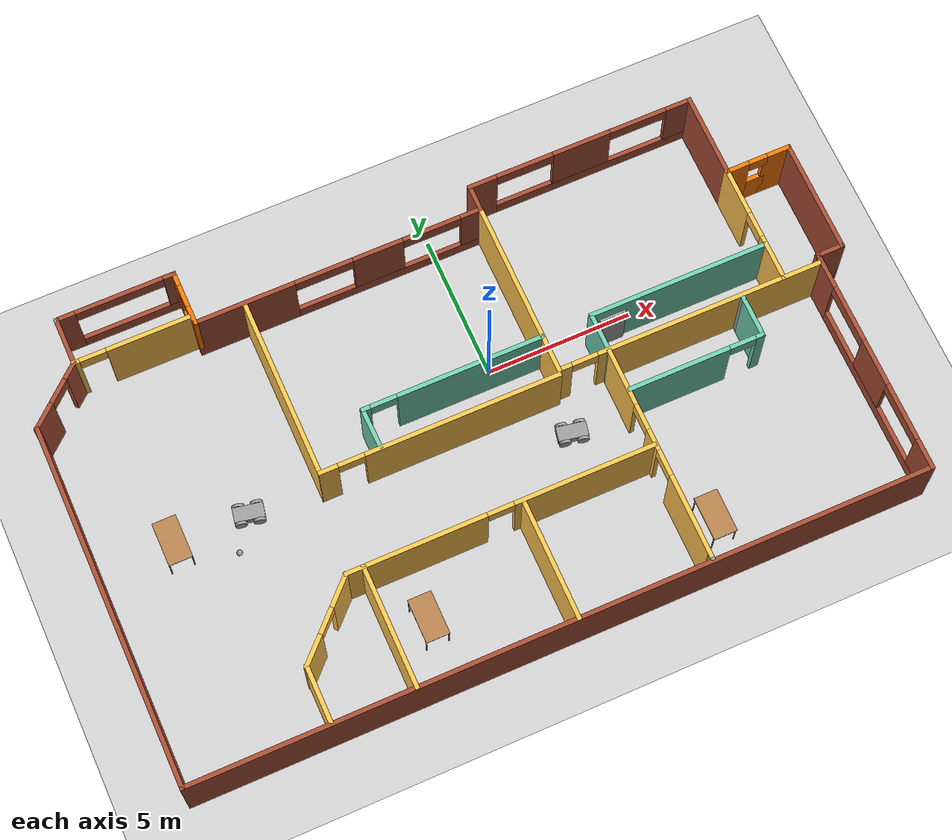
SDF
<sdf version="1.6">
 <world name="default">
  <plugin name="welcome_msg" filename="libwelcome_msg.so"/>
  <light name="sun" type="directional">
   <pose>0 0 10 0 -0 0</pose>
   <diffuse>0.8 0.8 0.8 1</diffuse>
   <specular>0.1 0.1 0.1 1</specular>
   <attenuation>
    <range>1000</range>
    <constant>0.9</constant>
    <linear>0.01</linear>
    <quadratic>0.001</quadratic>
   </attenuation>
   <direction>-0.5 0.5 -1</direction>
  </light>
  <model name="ground_plane">
   <static>1</static>
   <link name="link">
    <collision name="collision">
     <geometry><plane><normal>0 0 1</normal><size>100 100</size></plane></geometry>
     <surface><friction><ode><mu>100</mu><mu2>50</mu2></ode></friction></surface>
    </collision>
    <visual name="visual">
     <cast_shadows>0</cast_shadows>
     <geometry><plane><normal>0 0 1</normal><size>100 100</size></plane></geometry>
     <material>
      <script><uri>file://media/materials/scripts/gazebo.material</uri><name>Gazebo/Grey</name></script>
     </material>
    </visual>
   </link>
  </model>
  <gravity>0 0 -9.8</gravity>
  <magnetic_field>6e-06 2.3e-05 -4.2e-05</magnetic_field>
  <atmosphere type="adiabatic"/>
  <physics name="default_physics" default="0" type="ode">
   <max_step_size>0.001</max_step_size>
   <real_time_factor>1</real_time_factor>
   <real_time_update_rate>1000</real_time_update_rate>
  </physics>
  <scene><ambient>0.4 0.4 0.4 1</ambient><background>0.7 0.7 0.7 1</background><shadows>1</shadows></scene>
  <spherical_coordinates>
   <surface_model>EARTH_WGS84</surface_model>
   <latitude_deg>0</latitude_deg>
   <longitude_deg>0</longitude_deg>
   <elevation>0</elevation>
   <heading_deg>0</heading_deg>
  </spherical_coordinates>
  <model name="building">
   <pose>-1.18048 -1.54678 0 0 -0 0</pose>
   <link name="Door_9">
    <collision name="Door_9_Collision">
     <geometry><box><size>0.9 0.17 2</size></box></geometry>
     <pose>0 0 1 0 -0 0</pose>
    </collision>
    <visual name="Door_9_Visual">
     <pose>0 0 1 0 -0 0</pose>
     <geometry><box><size>0.9 0.17 2</size></box></geometry>
     <material>
      <script><uri>file://media/materials/scripts/gazebo.material</uri><name>Gazebo/Grey</name></script>
     </material>
    </visual>
    <pose>5.24635 1.02928 0 0 -0 0</pose>
   </link>
   <link name="Wall_10">
    <collision name="Wall_10_Collision">
     <geometry><box><size>1 0.15 2.5</size></box></geometry>
     <pose>0 0 1.25 0 -0 0</pose>
    </collision>
    <visual name="Wall_10_Visual">
     <pose>0 0 1.25 0 -0 0</pose>
     <geometry><box><size>1 0.15 2.5</size></box></geometry>
     <material>
      <script><uri>file://media/materials/scripts/gazebo.material</uri><name>Gazebo/Grey</name></script>
      <ambient>0.996078 0.47451 0.0196078 1</ambient>
     </material>
     <meta><layer>0</layer></meta>
    </visual>
    <pose>12.4404 3.92519 0 0 -0 0</pose>
   </link>
   <link name="Wall_11">
    <collision name="Wall_11_Collision">
     <geometry><box><size>4 0.15 2.5</size></box></geometry>
     <pose>0 0 1.25 0 -0 0</pose>
    </collision>
    <visual name="Wall_11_Visual">
     <pose>0 0 1.25 0 -0 0</pose>
     <geometry><box><size>4 0.15 2.5</size></box></geometry>
     <material>
      <script><uri>file://media/materials/scripts/gazebo.material</uri><name>Gazebo/Bricks</name></script>
      <ambient>0.996078 0.47451 0.0196078 1</ambient>
     </material>
     <meta><layer>0</layer></meta>
    </visual>
    <pose>12.8654 2.00019 0 0 0 -1.5708</pose>
   </link>
   <link name="Wall_12">
    <collision name="Wall_12_Collision">
     <geometry><box><size>1 0.15 2.5</size></box></geometry>
     <pose>0 0 1.25 0 -0 0</pose>
    </collision>
    <visual name="Wall_12_Visual">
     <pose>0 0 1.25 0 -0 0</pose>
     <geometry><box><size>1 0.15 2.5</size></box></geometry>
     <material>
      <script><uri>file://media/materials/scripts/gazebo.material</uri><name>Gazebo/Bricks</name></script>
      <ambient>0.996078 0.47451 0.0196078 1</ambient>
     </material>
     <meta><layer>0</layer></meta>
    </visual>
    <pose>12.4404 0.075189 0 0 -0 3.14159</pose>
   </link>
   <link name="Wall_13">
    <pose>12.0154 -3.84981 0 0 0 -1.5708</pose>
    <visual name="Wall_13_Visual_0">
     <pose>-3.35895 0 1.25 0 -0 0</pose>
     <geometry><box><size>1.28209 0.15 2.5</size></box></geometry>
     <material>
      <script><uri>file://media/materials/scripts/gazebo.material</uri><name>Gazebo/Bricks</name></script>
      <ambient>0.996078 0.47451 0.0196078 1</ambient>
     </material>
     <meta><layer>0</layer></meta>
    </visual>
    <collision name="Wall_13_Collision_0">
     <geometry><box><size>1.28209 0.15 2.5</size></box></geometry>
     <pose>-3.35895 0 1.25 0 -0 0</pose>
    </collision>
    <visual name="Wall_13_Visual_1">
     <pose>0.641045 0 0.25 0 -0 0</pose>
     <geometry><box><size>6.71791 0.15 0.5</size></box></geometry>
     <material>
      <script><uri>file://media/materials/scripts/gazebo.material</uri><name>Gazebo/Bricks</name></script>
      <ambient>0.996078 0.47451 0.0196078 1</ambient>
     </material>
     <meta><layer>0</layer></meta>
    </visual>
    <collision name="Wall_13_Collision_1">
     <geometry><box><size>6.71791 0.15 0.5</size></box></geometry>
     <pose>0.641045 0 0.25 0 -0 0</pose>
    </collision>
    <visual name="Wall_13_Visual_2">
     <pose>0.102981 0 1.5 0 -0 0</pose>
     <geometry><box><size>1.64178 0.15 2</size></box></geometry>
     <material>
      <script><uri>file://media/materials/scripts/gazebo.material</uri><name>Gazebo/Bricks</name></script>
      <ambient>0.996078 0.47451 0.0196078 1</ambient>
     </material>
     <meta><layer>0</layer></meta>
    </visual>
    <collision name="Wall_13_Collision_2">
     <geometry><box><size>1.64178 0.15 2</size></box></geometry>
     <pose>0.102981 0 1.5 0 -0 0</pose>
    </collision>
    <visual name="Wall_13_Visual_3">
     <pose>3.46194 0 1.5 0 -0 0</pose>
     <geometry><box><size>1.07613 0.15 2</size></box></geometry>
     <material>
      <script><uri>file://media/materials/scripts/gazebo.material</uri><name>Gazebo/Bricks</name></script>
      <ambient>0.996078 0.47451 0.0196078 1</ambient>
     </material>
     <meta><layer>0</layer></meta>
    </visual>
    <collision name="Wall_13_Collision_3">
     <geometry><box><size>1.07613 0.15 2</size></box></geometry>
     <pose>3.46194 0 1.5 0 -0 0</pose>
    </collision>
    <visual name="Wall_13_Visual_4">
     <pose>-1.71791 0 2.25 0 -0 0</pose>
     <geometry><box><size>2 0.15 0.5</size></box></geometry>
     <material>
      <script><uri>file://media/materials/scripts/gazebo.material</uri><name>Gazebo/Bricks</name></script>
      <ambient>0.996078 0.47451 0.0196078 1</ambient>
     </material>
     <meta><layer>0</layer></meta>
    </visual>
    <collision name="Wall_13_Collision_4">
     <geometry><box><size>2 0.15 0.5</size></box></geometry>
     <pose>-1.71791 0 2.25 0 -0 0</pose>
    </collision>
    <visual name="Wall_13_Visual_5">
     <pose>1.92387 0 2.25 0 -0 0</pose>
     <geometry><box><size>2 0.15 0.5</size></box></geometry>
     <material>
      <script><uri>file://media/materials/scripts/gazebo.material</uri><name>Gazebo/Bricks</name></script>
      <ambient>0.996078 0.47451 0.0196078 1</ambient>
     </material>
     <meta><layer>0</layer></meta>
    </visual>
    <collision name="Wall_13_Collision_5">
     <geometry><box><size>2 0.15 0.5</size></box></geometry>
     <pose>1.92387 0 2.25 0 -0 0</pose>
    </collision>
   </link>
   <link name="Wall_14">
    <collision name="Wall_14_Collision">
     <geometry><box><size>25 0.15 2.5</size></box></geometry>
     <pose>0 0 1.25 0 -0 0</pose>
    </collision>
    <visual name="Wall_14_Visual">
     <pose>0 0 1.25 0 -0 0</pose>
     <geometry><box><size>25 0.15 2.5</size></box></geometry>
     <material>
      <script><uri>file://media/materials/scripts/gazebo.material</uri><name>Gazebo/Bricks</name></script>
      <ambient>0.996078 0.47451 0.0196078 1</ambient>
     </material>
     <meta><layer>0</layer></meta>
    </visual>
    <pose>-0.409386 -7.775 0 0 0 -3.14158</pose>
   </link>
   <link name="Wall_15">
    <collision name="Wall_15_Collision">
     <geometry><box><size>12.5 0.15 2.5</size></box></geometry>
     <pose>0 0 1.25 0 -0 0</pose>
    </collision>
    <visual name="Wall_15_Visual">
     <pose>0 0 1.25 0 -0 0</pose>
     <geometry><box><size>12.5 0.15 2.5</size></box></geometry>
     <material>
      <script><uri>file://media/materials/scripts/gazebo.material</uri><name>Gazebo/Bricks</name></script>
      <ambient>0.996078 0.47451 0.0196078 1</ambient>
     </material>
     <meta><layer>0</layer></meta>
    </visual>
    <pose>-12.8344 -1.6 0 0 -0 1.57083</pose>
   </link>
   <link name="Wall_18">
    <collision name="Wall_18_Collision">
     <geometry><box><size>0.15 0.15 2.5</size></box></geometry>
     <pose>0 0 1.25 0 -0 0</pose>
    </collision>
    <visual name="Wall_18_Visual">
     <pose>0 0 1.25 0 -0 0</pose>
     <geometry><box><size>0.15 0.15 2.5</size></box></geometry>
     <material>
      <script><uri>file://media/materials/scripts/gazebo.material</uri><name>Gazebo/Grey</name></script>
      <ambient>1 1 1 1</ambient>
     </material>
     <meta><layer>0</layer></meta>
    </visual>
    <pose>-11.0156 7.76619 0 0 -0 0</pose>
   </link>
   <link name="Wall_2">
    <pose>-8.95963 7.77519 0 0 -0 0</pose>
    <visual name="Wall_2_Visual_0">
     <pose>-1.7146 0 1.25 0 -0 0</pose>
     <geometry><box><size>0.570799 0.15 2.5</size></box></geometry>
     <material>
      <script><uri>file://media/materials/scripts/gazebo.material</uri><name>Gazebo/Bricks</name></script>
      <ambient>0.996078 0.47451 0.0196078 1</ambient>
     </material>
     <meta><layer>0</layer></meta>
    </visual>
    <collision name="Wall_2_Collision_0">
     <geometry><box><size>0.570799 0.15 2.5</size></box></geometry>
     <pose>-1.7146 0 1.25 0 -0 0</pose>
    </collision>
    <visual name="Wall_2_Visual_1">
     <pose>0.285399 0 0.25 0 -0 0</pose>
     <geometry><box><size>3.4292 0.15 0.5</size></box></geometry>
     <material>
      <script><uri>file://media/materials/scripts/gazebo.material</uri><name>Gazebo/Bricks</name></script>
      <ambient>0.996078 0.47451 0.0196078 1</ambient>
     </material>
     <meta><layer>0</layer></meta>
    </visual>
    <collision name="Wall_2_Collision_1">
     <geometry><box><size>3.4292 0.15 0.5</size></box></geometry>
     <pose>0.285399 0 0.25 0 -0 0</pose>
    </collision>
    <visual name="Wall_2_Visual_2">
     <pose>1.7754 0 1.5 0 -0 0</pose>
     <geometry><box><size>0.449201 0.15 2</size></box></geometry>
     <material>
      <script><uri>file://media/materials/scripts/gazebo.material</uri><name>Gazebo/Bricks</name></script>
      <ambient>0.996078 0.47451 0.0196078 1</ambient>
     </material>
     <meta><layer>0</layer></meta>
    </visual>
    <collision name="Wall_2_Collision_2">
     <geometry><box><size>0.449201 0.15 2</size></box></geometry>
     <pose>1.7754 0 1.5 0 -0 0</pose>
    </collision>
    <visual name="Wall_2_Visual_3">
     <pose>0.060799 0 2.25 0 -0 0</pose>
     <geometry><box><size>2.98 0.15 0.5</size></box></geometry>
     <material>
      <script><uri>file://media/materials/scripts/gazebo.material</uri><name>Gazebo/Bricks</name></script>
      <ambient>0.996078 0.47451 0.0196078 1</ambient>
     </material>
     <meta><layer>0</layer></meta>
    </visual>
    <collision name="Wall_2_Collision_3">
     <geometry><box><size>2.98 0.15 0.5</size></box></geometry>
     <pose>0.060799 0 2.25 0 -0 0</pose>
    </collision>
   </link>
   <link name="Wall_21">
    <collision name="Wall_21_Collision">
     <geometry><box><size>1.72887 0.15 2.5</size></box></geometry>
     <pose>0 0 1.25 0 -0 0</pose>
    </collision>
    <visual name="Wall_21_Visual">
     <pose>0 0 1.25 0 -0 0</pose>
     <geometry><box><size>1.72887 0.15 2.5</size></box></geometry>
     <material>
      <script><uri>file://media/materials/scripts/gazebo.material</uri><name>Gazebo/Bricks</name></script>
      <ambient>0.996078 0.47451 0.0196078 1</ambient>
     </material>
     <meta><layer>0</layer></meta>
    </visual>
    <pose>-11.0156 6.97669 0 0 0 -1.5708</pose>
   </link>
   <link name="Wall_22">
    <pose>-11.9251 5.38119 0 0 0 -2.41645</pose>
    <visual name="Wall_22_Visual_0">
     <pose>-0.957133 0 1.25 0 -0 0</pose>
     <geometry><box><size>0.665888 0.15 2.5</size></box></geometry>
     <material>
      <script><uri>file://media/materials/scripts/gazebo.material</uri><name>Gazebo/Bricks</name></script>
      <ambient>0.996078 0.47451 0.0196078 1</ambient>
     </material>
     <meta><layer>0</layer></meta>
    </visual>
    <collision name="Wall_22_Collision_0">
     <geometry><box><size>0.665888 0.15 2.5</size></box></geometry>
     <pose>-0.957133 0 1.25 0 -0 0</pose>
    </collision>
    <visual name="Wall_22_Visual_1">
     <pose>0.782944 0 1.25 0 -0 0</pose>
     <geometry><box><size>1.01427 0.15 2.5</size></box></geometry>
     <material>
      <script><uri>file://media/materials/scripts/gazebo.material</uri><name>Gazebo/Bricks</name></script>
      <ambient>0.996078 0.47451 0.0196078 1</ambient>
     </material>
     <meta><layer>0</layer></meta>
    </visual>
    <collision name="Wall_22_Collision_1">
     <geometry><box><size>1.01427 0.15 2.5</size></box></geometry>
     <pose>0.782944 0 1.25 0 -0 0</pose>
    </collision>
    <visual name="Wall_22_Visual_2">
     <pose>-0.174189 0 2.25 0 -0 0</pose>
     <geometry><box><size>0.9 0.15 0.5</size></box></geometry>
     <material>
      <script><uri>file://media/materials/scripts/gazebo.material</uri><name>Gazebo/Bricks</name></script>
      <ambient>0.996078 0.47451 0.0196078 1</ambient>
     </material>
     <meta><layer>0</layer></meta>
    </visual>
    <collision name="Wall_22_Collision_2">
     <geometry><box><size>0.9 0.15 0.5</size></box></geometry>
     <pose>-0.174189 0 2.25 0 -0 0</pose>
    </collision>
   </link>
   <link name="Wall_24">
    <collision name="Wall_24_Collision">
     <geometry><box><size>6.25 0.15 2.5</size></box></geometry>
     <pose>0 0 1.25 0 -0 0</pose>
    </collision>
    <visual name="Wall_24_Visual">
     <pose>0 0 1.25 0 -0 0</pose>
     <geometry><box><size>6.25 0.15 2.5</size></box></geometry>
     <material>
      <script><uri>file://media/materials/scripts/gazebo.material</uri><name>Gazebo/Grey</name></script>
      <ambient>1 0.764706 0.305882 1</ambient>
     </material>
     <meta><layer>0</layer></meta>
    </visual>
    <pose>2.81537 2.87519 0 0 0 -1.5708</pose>
   </link>
   <link name="Wall_25">
    <pose>7.36561 -0.174999 0 0 0 -4.1e-05</pose>
    <visual name="Wall_25_Visual_0">
     <pose>-4.36759 0 1.25 0 -0 0</pose>
     <geometry><box><size>0.514816 0.15 2.5</size></box></geometry>
     <material>
      <script><uri>file://media/materials/scripts/gazebo.material</uri><name>Gazebo/Grey</name></script>
      <ambient>1 0.764706 0.305882 1</ambient>
     </material>
     <meta><layer>0</layer></meta>
    </visual>
    <collision name="Wall_25_Collision_0">
     <geometry><box><size>0.514816 0.15 2.5</size></box></geometry>
     <pose>-4.36759 0 1.25 0 -0 0</pose>
    </collision>
    <visual name="Wall_25_Visual_1">
     <pose>0.707408 0 1.25 0 -0 0</pose>
     <geometry><box><size>7.83518 0.15 2.5</size></box></geometry>
     <material>
      <script><uri>file://media/materials/scripts/gazebo.material</uri><name>Gazebo/Grey</name></script>
      <ambient>1 0.764706 0.305882 1</ambient>
     </material>
     <meta><layer>0</layer></meta>
    </visual>
    <collision name="Wall_25_Collision_1">
     <geometry><box><size>7.83518 0.15 2.5</size></box></geometry>
     <pose>0.707408 0 1.25 0 -0 0</pose>
    </collision>
    <visual name="Wall_25_Visual_2">
     <pose>-3.66018 0 2.25 0 -0 0</pose>
     <geometry><box><size>0.9 0.15 0.5</size></box></geometry>
     <material>
      <script><uri>file://media/materials/scripts/gazebo.material</uri><name>Gazebo/Grey</name></script>
      <ambient>1 0.764706 0.305882 1</ambient>
     </material>
     <meta><layer>0</layer></meta>
    </visual>
    <collision name="Wall_25_Collision_2">
     <geometry><box><size>0.9 0.15 0.5</size></box></geometry>
     <pose>-3.66018 0 2.25 0 -0 0</pose>
    </collision>
   </link>
   <link name="Wall_27">
    <collision name="Wall_27_Collision">
     <geometry><box><size>6.25 0.15 2.5</size></box></geometry>
     <pose>0 0 1.25 0 -0 0</pose>
    </collision>
    <visual name="Wall_27_Visual">
     <pose>0 0 1.25 0 -0 0</pose>
     <geometry><box><size>6.25 0.15 2.5</size></box></geometry>
     <material>
      <script><uri>file://media/materials/scripts/gazebo.material</uri><name>Gazebo/Grey</name></script>
      <ambient>1 0.764706 0.305882 1</ambient>
     </material>
     <meta><layer>0</layer></meta>
    </visual>
    <pose>-5.35916 2.72749 0 0 0 -1.5708</pose>
   </link>
   <link name="Wall_28">
    <pose>-1.29552 -0.32251 0 0 -0 0</pose>
    <visual name="Wall_28_Visual_0">
     <pose>-3.79542 0 1.25 0 -0 0</pose>
     <geometry><box><size>0.659156 0.15 2.5</size></box></geometry>
     <material>
      <script><uri>file://media/materials/scripts/gazebo.material</uri><name>Gazebo/Grey</name></script>
      <ambient>1 0.764706 0.305882 1</ambient>
     </material>
     <meta><layer>0</layer></meta>
    </visual>
    <collision name="Wall_28_Collision_0">
     <geometry><box><size>0.659156 0.15 2.5</size></box></geometry>
     <pose>-3.79542 0 1.25 0 -0 0</pose>
    </collision>
    <visual name="Wall_28_Visual_1">
     <pose>0.779578 0 1.25 0 -0 0</pose>
     <geometry><box><size>6.69084 0.15 2.5</size></box></geometry>
     <material>
      <script><uri>file://media/materials/scripts/gazebo.material</uri><name>Gazebo/Grey</name></script>
      <ambient>1 0.764706 0.305882 1</ambient>
     </material>
     <meta><layer>0</layer></meta>
    </visual>
    <collision name="Wall_28_Collision_1">
     <geometry><box><size>6.69084 0.15 2.5</size></box></geometry>
     <pose>0.779578 0 1.25 0 -0 0</pose>
    </collision>
    <visual name="Wall_28_Visual_2">
     <pose>-3.01584 0 2.25 0 -0 0</pose>
     <geometry><box><size>0.9 0.15 0.5</size></box></geometry>
     <material>
      <script><uri>file://media/materials/scripts/gazebo.material</uri><name>Gazebo/Grey</name></script>
      <ambient>1 0.764706 0.305882 1</ambient>
     </material>
     <meta><layer>0</layer></meta>
    </visual>
    <collision name="Wall_28_Collision_2">
     <geometry><box><size>0.9 0.15 0.5</size></box></geometry>
     <pose>-3.01584 0 2.25 0 -0 0</pose>
    </collision>
   </link>
   <link name="Wall_3">
    <pose>-7.03463 6.85019 0 0 0 -1.5708</pose>
    <visual name="Wall_3_Visual_0">
     <pose>-0.742492 0 1.25 0 -0 0</pose>
     <geometry><box><size>0.515016 0.15 2.5</size></box></geometry>
     <material>
      <script><uri>file://media/materials/scripts/gazebo.material</uri><name>Gazebo/Grey</name></script>
      <ambient>0.996078 0.47451 0.0196078 1</ambient>
     </material>
     <meta><layer>0</layer></meta>
    </visual>
    <collision name="Wall_3_Collision_0">
     <geometry><box><size>0.515016 0.15 2.5</size></box></geometry>
     <pose>-0.742492 0 1.25 0 -0 0</pose>
    </collision>
    <visual name="Wall_3_Visual_1">
     <pose>0.257508 0 0.25 0 -0 0</pose>
     <geometry><box><size>1.48498 0.15 0.5</size></box></geometry>
     <material>
      <script><uri>file://media/materials/scripts/gazebo.material</uri><name>Gazebo/Grey</name></script>
      <ambient>0.996078 0.47451 0.0196078 1</ambient>
     </material>
     <meta><layer>0</layer></meta>
    </visual>
    <collision name="Wall_3_Collision_1">
     <geometry><box><size>1.48498 0.15 0.5</size></box></geometry>
     <pose>0.257508 0 0.25 0 -0 0</pose>
    </collision>
    <visual name="Wall_3_Visual_2">
     <pose>0.657508 0 1.5 0 -0 0</pose>
     <geometry><box><size>0.684984 0.15 2</size></box></geometry>
     <material>
      <script><uri>file://media/materials/scripts/gazebo.material</uri><name>Gazebo/Grey</name></script>
      <ambient>0.996078 0.47451 0.0196078 1</ambient>
     </material>
     <meta><layer>0</layer></meta>
    </visual>
    <collision name="Wall_3_Collision_2">
     <geometry><box><size>0.684984 0.15 2</size></box></geometry>
     <pose>0.657508 0 1.5 0 -0 0</pose>
    </collision>
    <visual name="Wall_3_Visual_3">
     <pose>-0.084984 0 2.25 0 -0 0</pose>
     <geometry><box><size>0.8 0.15 0.5</size></box></geometry>
     <material>
      <script><uri>file://media/materials/scripts/gazebo.material</uri><name>Gazebo/Grey</name></script>
      <ambient>0.996078 0.47451 0.0196078 1</ambient>
     </material>
     <meta><layer>0</layer></meta>
    </visual>
    <collision name="Wall_3_Collision_3">
     <geometry><box><size>0.8 0.15 0.5</size></box></geometry>
     <pose>-0.084984 0 2.25 0 -0 0</pose>
    </collision>
   </link>
   <link name="Wall_30">
    <pose>4.52737 -3.91681 0 0 0 -1.5708</pose>
    <visual name="Wall_30_Visual_0">
     <pose>-2.73062 0 1.25 0 -0 0</pose>
     <geometry><box><size>2.03875 0.15 2.5</size></box></geometry>
     <material>
      <script><uri>file://media/materials/scripts/gazebo.material</uri><name>Gazebo/Grey</name></script>
      <ambient>1 0.764706 0.305882 1</ambient>
     </material>
     <meta><layer>0</layer></meta>
    </visual>
    <collision name="Wall_30_Collision_0">
     <geometry><box><size>2.03875 0.15 2.5</size></box></geometry>
     <pose>-2.73062 0 1.25 0 -0 0</pose>
    </collision>
    <visual name="Wall_30_Visual_1">
     <pose>-0.433439 0 1.25 0 -0 0</pose>
     <geometry><box><size>0.755616 0.15 2.5</size></box></geometry>
     <material>
      <script><uri>file://media/materials/scripts/gazebo.material</uri><name>Gazebo/Grey</name></script>
      <ambient>1 0.764706 0.305882 1</ambient>
     </material>
     <meta><layer>0</layer></meta>
    </visual>
    <collision name="Wall_30_Collision_1">
     <geometry><box><size>0.755616 0.15 2.5</size></box></geometry>
     <pose>-0.433439 0 1.25 0 -0 0</pose>
    </collision>
    <visual name="Wall_30_Visual_2">
     <pose>2.29718 0 1.25 0 -0 0</pose>
     <geometry><box><size>2.90563 0.15 2.5</size></box></geometry>
     <material>
      <script><uri>file://media/materials/scripts/gazebo.material</uri><name>Gazebo/Grey</name></script>
      <ambient>1 0.764706 0.305882 1</ambient>
     </material>
     <meta><layer>0</layer></meta>
    </visual>
    <collision name="Wall_30_Collision_2">
     <geometry><box><size>2.90563 0.15 2.5</size></box></geometry>
     <pose>2.29718 0 1.25 0 -0 0</pose>
    </collision>
    <visual name="Wall_30_Visual_3">
     <pose>-1.26125 0 2.25 0 -0 0</pose>
     <geometry><box><size>0.9 0.15 0.5</size></box></geometry>
     <material>
      <script><uri>file://media/materials/scripts/gazebo.material</uri><name>Gazebo/Grey</name></script>
      <ambient>1 0.764706 0.305882 1</ambient>
     </material>
     <meta><layer>0</layer></meta>
    </visual>
    <collision name="Wall_30_Collision_3">
     <geometry><box><size>0.9 0.15 0.5</size></box></geometry>
     <pose>-1.26125 0 2.25 0 -0 0</pose>
    </collision>
    <visual name="Wall_30_Visual_4">
     <pose>0.394369 0 2.25 0 -0 0</pose>
     <geometry><box><size>0.9 0.15 0.5</size></box></geometry>
     <material>
      <script><uri>file://media/materials/scripts/gazebo.material</uri><name>Gazebo/Grey</name></script>
      <ambient>1 0.764706 0.305882 1</ambient>
     </material>
     <meta><layer>0</layer></meta>
    </visual>
    <collision name="Wall_30_Collision_4">
     <geometry><box><size>0.9 0.15 0.5</size></box></geometry>
     <pose>0.394369 0 2.25 0 -0 0</pose>
    </collision>
   </link>
   <link name="Wall_32">
    <collision name="Wall_32_Collision">
     <geometry><box><size>0.25 0.15 2.5</size></box></geometry>
     <pose>0 0 1.25 0 -0 0</pose>
    </collision>
    <visual name="Wall_32_Visual">
     <pose>0 0 1.25 0 -0 0</pose>
     <geometry><box><size>0.25 0.15 2.5</size></box></geometry>
     <material>
      <script><uri>file://media/materials/scripts/gazebo.material</uri><name>Gazebo/Grey</name></script>
      <ambient>1 1 1 1</ambient>
     </material>
     <meta><layer>0</layer></meta>
    </visual>
    <pose>4.52743 -7.64189 0 0 0 -1.56959</pose>
   </link>
   <link name="Wall_34">
    <pose>-0.701627 -3.64881 0 0 -0 3.14159</pose>
    <visual name="Wall_34_Visual_0">
     <pose>-2.83618 0 1.25 0 -0 0</pose>
     <geometry><box><size>4.82764 0.15 2.5</size></box></geometry>
     <material>
      <script><uri>file://media/materials/scripts/gazebo.material</uri><name>Gazebo/Grey</name></script>
      <ambient>1 0.764706 0.305882 1</ambient>
     </material>
     <meta><layer>0</layer></meta>
    </visual>
    <collision name="Wall_34_Collision_0">
     <geometry><box><size>4.82764 0.15 2.5</size></box></geometry>
     <pose>-2.83618 0 1.25 0 -0 0</pose>
    </collision>
    <visual name="Wall_34_Visual_1">
     <pose>2.86382 0 1.25 0 -0 0</pose>
     <geometry><box><size>4.77236 0.15 2.5</size></box></geometry>
     <material>
      <script><uri>file://media/materials/scripts/gazebo.material</uri><name>Gazebo/Grey</name></script>
      <ambient>1 0.764706 0.305882 1</ambient>
     </material>
     <meta><layer>0</layer></meta>
    </visual>
    <collision name="Wall_34_Collision_1">
     <geometry><box><size>4.77236 0.15 2.5</size></box></geometry>
     <pose>2.86382 0 1.25 0 -0 0</pose>
    </collision>
    <visual name="Wall_34_Visual_2">
     <pose>0.02764 0 2.25 0 -0 0</pose>
     <geometry><box><size>0.9 0.15 0.5</size></box></geometry>
     <material>
      <script><uri>file://media/materials/scripts/gazebo.material</uri><name>Gazebo/Grey</name></script>
      <ambient>1 0.764706 0.305882 1</ambient>
     </material>
     <meta><layer>0</layer></meta>
    </visual>
    <collision name="Wall_34_Collision_2">
     <geometry><box><size>0.9 0.15 0.5</size></box></geometry>
     <pose>0.02764 0 2.25 0 -0 0</pose>
    </collision>
   </link>
   <link name="Wall_35">
    <pose>-6.97252 -4.74494 0 0 0 -2.35608</pose>
    <visual name="Wall_35_Visual_0">
     <pose>-1.02165 0 1.25 0 -0 0</pose>
     <geometry><box><size>1.20669 0.15 2.5</size></box></geometry>
     <material>
      <script><uri>file://media/materials/scripts/gazebo.material</uri><name>Gazebo/Grey</name></script>
      <ambient>1 0.764706 0.305882 1</ambient>
     </material>
     <meta><layer>0</layer></meta>
    </visual>
    <collision name="Wall_35_Collision_0">
     <geometry><box><size>1.20669 0.15 2.5</size></box></geometry>
     <pose>-1.02165 0 1.25 0 -0 0</pose>
    </collision>
    <visual name="Wall_35_Visual_1">
     <pose>1.05335 0 1.25 0 -0 0</pose>
     <geometry><box><size>1.14331 0.15 2.5</size></box></geometry>
     <material>
      <script><uri>file://media/materials/scripts/gazebo.material</uri><name>Gazebo/Grey</name></script>
      <ambient>1 0.764706 0.305882 1</ambient>
     </material>
     <meta><layer>0</layer></meta>
    </visual>
    <collision name="Wall_35_Collision_1">
     <geometry><box><size>1.14331 0.15 2.5</size></box></geometry>
     <pose>1.05335 0 1.25 0 -0 0</pose>
    </collision>
    <visual name="Wall_35_Visual_2">
     <pose>0.031691 0 2.25 0 -0 0</pose>
     <geometry><box><size>0.9 0.15 0.5</size></box></geometry>
     <material>
      <script><uri>file://media/materials/scripts/gazebo.material</uri><name>Gazebo/Grey</name></script>
      <ambient>1 0.764706 0.305882 1</ambient>
     </material>
     <meta><layer>0</layer></meta>
    </visual>
    <collision name="Wall_35_Collision_2">
     <geometry><box><size>0.9 0.15 0.5</size></box></geometry>
     <pose>0.031691 0 2.25 0 -0 0</pose>
    </collision>
   </link>
   <link name="Wall_36">
    <collision name="Wall_36_Collision">
     <geometry><box><size>2 0.15 2.5</size></box></geometry>
     <pose>0 0 1.25 0 -0 0</pose>
    </collision>
    <visual name="Wall_36_Visual">
     <pose>0 0 1.25 0 -0 0</pose>
     <geometry><box><size>2 0.15 2.5</size></box></geometry>
     <material>
      <script><uri>file://media/materials/scripts/gazebo.material</uri><name>Gazebo/Grey</name></script>
      <ambient>1 0.764706 0.305882 1</ambient>
     </material>
     <meta><layer>0</layer></meta>
    </visual>
    <pose>-8.06841 -6.76607 0 0 0 -1.5708</pose>
   </link>
   <link name="Wall_38">
    <collision name="Wall_38_Collision">
     <geometry><box><size>4.25 0.15 2.5</size></box></geometry>
     <pose>0 0 1.25 0 -0 0</pose>
    </collision>
    <visual name="Wall_38_Visual">
     <pose>0 0 1.25 0 -0 0</pose>
     <geometry><box><size>4.25 0.15 2.5</size></box></geometry>
     <material>
      <script><uri>file://media/materials/scripts/gazebo.material</uri><name>Gazebo/Grey</name></script>
      <ambient>1 0.764706 0.305882 1</ambient>
     </material>
     <meta><layer>0</layer></meta>
    </visual>
    <pose>-5.30163 -5.71081 0 0 0 -1.5708</pose>
   </link>
   <link name="Wall_4">
    <pose>-2.10963 5.92519 0 0 -0 0</pose>
    <visual name="Wall_4_Visual_0">
     <pose>-3.26273 0 1.25 0 -0 0</pose>
     <geometry><box><size>3.47454 0.15 2.5</size></box></geometry>
     <material>
      <script><uri>file://media/materials/scripts/gazebo.material</uri><name>Gazebo/Bricks</name></script>
      <ambient>0.996078 0.47451 0.0196078 1</ambient>
     </material>
     <meta><layer>0</layer></meta>
    </visual>
    <collision name="Wall_4_Collision_0">
     <geometry><box><size>3.47454 0.15 2.5</size></box></geometry>
     <pose>-3.26273 0 1.25 0 -0 0</pose>
    </collision>
    <visual name="Wall_4_Visual_1">
     <pose>1.73727 0 0.25 0 -0 0</pose>
     <geometry><box><size>6.52546 0.15 0.5</size></box></geometry>
     <material>
      <script><uri>file://media/materials/scripts/gazebo.material</uri><name>Gazebo/Bricks</name></script>
      <ambient>0.996078 0.47451 0.0196078 1</ambient>
     </material>
     <meta><layer>0</layer></meta>
    </visual>
    <collision name="Wall_4_Collision_1">
     <geometry><box><size>6.52546 0.15 0.5</size></box></geometry>
     <pose>1.73727 0 0.25 0 -0 0</pose>
    </collision>
    <visual name="Wall_4_Visual_2">
     <pose>1.34236 0 1.5 0 -0 0</pose>
     <geometry><box><size>1.73563 0.15 2</size></box></geometry>
     <material>
      <script><uri>file://media/materials/scripts/gazebo.material</uri><name>Gazebo/Bricks</name></script>
      <ambient>0.996078 0.47451 0.0196078 1</ambient>
     </material>
     <meta><layer>0</layer></meta>
    </visual>
    <collision name="Wall_4_Collision_2">
     <geometry><box><size>1.73563 0.15 2</size></box></geometry>
     <pose>1.34236 0 1.5 0 -0 0</pose>
    </collision>
    <visual name="Wall_4_Visual_3">
     <pose>4.60509 0 1.5 0 -0 0</pose>
     <geometry><box><size>0.789828 0.15 2</size></box></geometry>
     <material>
      <script><uri>file://media/materials/scripts/gazebo.material</uri><name>Gazebo/Bricks</name></script>
      <ambient>0.996078 0.47451 0.0196078 1</ambient>
     </material>
     <meta><layer>0</layer></meta>
    </visual>
    <collision name="Wall_4_Collision_3">
     <geometry><box><size>0.789828 0.15 2</size></box></geometry>
     <pose>4.60509 0 1.5 0 -0 0</pose>
    </collision>
    <visual name="Wall_4_Visual_4">
     <pose>-0.525461 0 2.25 0 -0 0</pose>
     <geometry><box><size>2 0.15 0.5</size></box></geometry>
     <material>
      <script><uri>file://media/materials/scripts/gazebo.material</uri><name>Gazebo/Bricks</name></script>
      <ambient>0.996078 0.47451 0.0196078 1</ambient>
     </material>
     <meta><layer>0</layer></meta>
    </visual>
    <collision name="Wall_4_Collision_4">
     <geometry><box><size>2 0.15 0.5</size></box></geometry>
     <pose>-0.525461 0 2.25 0 -0 0</pose>
    </collision>
    <visual name="Wall_4_Visual_5">
     <pose>3.21017 0 2.25 0 -0 0</pose>
     <geometry><box><size>2 0.15 0.5</size></box></geometry>
     <material>
      <script><uri>file://media/materials/scripts/gazebo.material</uri><name>Gazebo/Bricks</name></script>
      <ambient>0.996078 0.47451 0.0196078 1</ambient>
     </material>
     <meta><layer>0</layer></meta>
    </visual>
    <collision name="Wall_4_Collision_5">
     <geometry><box><size>2 0.15 0.5</size></box></geometry>
     <pose>3.21017 0 2.25 0 -0 0</pose>
    </collision>
   </link>
   <link name="Wall_40">
    <collision name="Wall_40_Collision">
     <geometry><box><size>4.25 0.15 2.5</size></box></geometry>
     <pose>0 0 1.25 0 -0 0</pose>
    </collision>
    <visual name="Wall_40_Visual">
     <pose>0 0 1.25 0 -0 0</pose>
     <geometry><box><size>4.25 0.15 2.5</size></box></geometry>
     <material>
      <script><uri>file://media/materials/scripts/gazebo.material</uri><name>Gazebo/Grey</name></script>
      <ambient>1 0.764706 0.305882 1</ambient>
     </material>
     <meta><layer>0</layer></meta>
    </visual>
    <pose>0.021373 -5.72281 0 0 0 -1.5708</pose>
   </link>
   <link name="Wall_42">
    <pose>10.6656 1.875 0 0 0 -1.57068</pose>
    <visual name="Wall_42_Visual_0">
     <pose>-1.27509 0 1.25 0 -0 0</pose>
     <geometry><box><size>1.69982 0.15 2.5</size></box></geometry>
     <material>
      <script><uri>file://media/materials/scripts/gazebo.material</uri><name>Gazebo/Grey</name></script>
      <ambient>1 0.764706 0.305882 1</ambient>
     </material>
     <meta><layer>0</layer></meta>
    </visual>
    <collision name="Wall_42_Collision_0">
     <geometry><box><size>1.69982 0.15 2.5</size></box></geometry>
     <pose>-1.27509 0 1.25 0 -0 0</pose>
    </collision>
    <visual name="Wall_42_Visual_1">
     <pose>1.29991 0 1.25 0 -0 0</pose>
     <geometry><box><size>1.65018 0.15 2.5</size></box></geometry>
     <material>
      <script><uri>file://media/materials/scripts/gazebo.material</uri><name>Gazebo/Grey</name></script>
      <ambient>1 0.764706 0.305882 1</ambient>
     </material>
     <meta><layer>0</layer></meta>
    </visual>
    <collision name="Wall_42_Collision_1">
     <geometry><box><size>1.65018 0.15 2.5</size></box></geometry>
     <pose>1.29991 0 1.25 0 -0 0</pose>
    </collision>
    <visual name="Wall_42_Visual_2">
     <pose>0.024819 0 2.25 0 -0 0</pose>
     <geometry><box><size>0.9 0.15 0.5</size></box></geometry>
     <material>
      <script><uri>file://media/materials/scripts/gazebo.material</uri><name>Gazebo/Grey</name></script>
      <ambient>1 0.764706 0.305882 1</ambient>
     </material>
     <meta><layer>0</layer></meta>
    </visual>
    <collision name="Wall_42_Collision_2">
     <geometry><box><size>0.9 0.15 0.5</size></box></geometry>
     <pose>0.024819 0 2.25 0 -0 0</pose>
    </collision>
   </link>
   <link name="Wall_49">
    <collision name="Wall_49_Collision">
     <geometry><box><size>0.15 0.15 2.5</size></box></geometry>
     <pose>0 0 1.25 0 -0 0</pose>
    </collision>
    <visual name="Wall_49_Visual">
     <pose>0 0 1.25 0 -0 0</pose>
     <geometry><box><size>0.15 0.15 2.5</size></box></geometry>
     <material>
      <script><uri>file://media/materials/scripts/gazebo.material</uri><name>Gazebo/Grey</name></script>
      <ambient>1 1 1 1</ambient>
     </material>
     <meta><layer>0</layer></meta>
    </visual>
    <pose>9.18137 -0.314811 0 0 -0 0</pose>
   </link>
   <link name="Wall_5">
    <collision name="Wall_5_Collision">
     <geometry><box><size>1 0.15 2.5</size></box></geometry>
     <pose>0 0 1.25 0 -0 0</pose>
    </collision>
    <visual name="Wall_5_Visual">
     <pose>0 0 1.25 0 -0 0</pose>
     <geometry><box><size>1 0.15 2.5</size></box></geometry>
     <material>
      <script><uri>file://media/materials/scripts/gazebo.material</uri><name>Gazebo/Bricks</name></script>
      <ambient>0.996078 0.47451 0.0196078 1</ambient>
     </material>
     <meta><layer>0</layer></meta>
    </visual>
    <pose>2.81537 6.35019 0 0 -0 1.5708</pose>
   </link>
   <link name="Wall_56">
    <collision name="Wall_56_Collision">
     <geometry><box><size>1.5 0.15 2.5</size></box></geometry>
     <pose>0 0 1.25 0 -0 0</pose>
    </collision>
    <visual name="Wall_56_Visual">
     <pose>0 0 1.25 0 -0 0</pose>
     <geometry><box><size>1.5 0.15 2.5</size></box></geometry>
     <material>
      <script><uri>file://media/materials/scripts/gazebo.material</uri><name>Gazebo/Grey</name></script>
      <ambient>0.435294 0.796078 0.67451 1</ambient>
     </material>
     <meta><layer>0</layer></meta>
    </visual>
    <pose>-3.32584 0.394189 0 0 -0 1.58593</pose>
   </link>
   <link name="Wall_58">
    <pose>-0.275843 1.06919 0 0 -0 0</pose>
    <visual name="Wall_58_Visual_0">
     <pose>-2.96525 0 1.25 0 -0 0</pose>
     <geometry><box><size>0.319491 0.15 2.5</size></box></geometry>
     <material>
      <script><uri>file://media/materials/scripts/gazebo.material</uri><name>Gazebo/Grey</name></script>
      <ambient>0.435294 0.796078 0.67451 1</ambient>
     </material>
     <meta><layer>0</layer></meta>
    </visual>
    <collision name="Wall_58_Collision_0">
     <geometry><box><size>0.319491 0.15 2.5</size></box></geometry>
     <pose>-2.96525 0 1.25 0 -0 0</pose>
    </collision>
    <visual name="Wall_58_Visual_1">
     <pose>0.609745 0 1.25 0 -0 0</pose>
     <geometry><box><size>5.03051 0.15 2.5</size></box></geometry>
     <material>
      <script><uri>file://media/materials/scripts/gazebo.material</uri><name>Gazebo/Grey</name></script>
      <ambient>0.435294 0.796078 0.67451 1</ambient>
     </material>
     <meta><layer>0</layer></meta>
    </visual>
    <collision name="Wall_58_Collision_1">
     <geometry><box><size>5.03051 0.15 2.5</size></box></geometry>
     <pose>0.609745 0 1.25 0 -0 0</pose>
    </collision>
    <visual name="Wall_58_Visual_2">
     <pose>-2.35551 0 2.25 0 -0 0</pose>
     <geometry><box><size>0.9 0.15 0.5</size></box></geometry>
     <material>
      <script><uri>file://media/materials/scripts/gazebo.material</uri><name>Gazebo/Grey</name></script>
      <ambient>0.435294 0.796078 0.67451 1</ambient>
     </material>
     <meta><layer>0</layer></meta>
    </visual>
    <collision name="Wall_58_Collision_2">
     <geometry><box><size>0.9 0.15 0.5</size></box></geometry>
     <pose>-2.35551 0 2.25 0 -0 0</pose>
    </collision>
   </link>
   <link name="Wall_6">
    <pose>6.74037 6.77519 0 0 -0 0</pose>
    <visual name="Wall_6_Visual_0">
     <pose>-3.49033 0 1.25 0 -0 0</pose>
     <geometry><box><size>1.01933 0.15 2.5</size></box></geometry>
     <material>
      <script><uri>file://media/materials/scripts/gazebo.material</uri><name>Gazebo/Bricks</name></script>
      <ambient>0.996078 0.47451 0.0196078 1</ambient>
     </material>
     <meta><layer>0</layer></meta>
    </visual>
    <collision name="Wall_6_Collision_0">
     <geometry><box><size>1.01933 0.15 2.5</size></box></geometry>
     <pose>-3.49033 0 1.25 0 -0 0</pose>
    </collision>
    <visual name="Wall_6_Visual_1">
     <pose>0.509666 0 0.25 0 -0 0</pose>
     <geometry><box><size>6.98067 0.15 0.5</size></box></geometry>
     <material>
      <script><uri>file://media/materials/scripts/gazebo.material</uri><name>Gazebo/Bricks</name></script>
      <ambient>0.996078 0.47451 0.0196078 1</ambient>
     </material>
     <meta><layer>0</layer></meta>
    </visual>
    <collision name="Wall_6_Collision_1">
     <geometry><box><size>6.98067 0.15 0.5</size></box></geometry>
     <pose>0.509666 0 0.25 0 -0 0</pose>
    </collision>
    <visual name="Wall_6_Visual_2">
     <pose>0.037578 0 1.5 0 -0 0</pose>
     <geometry><box><size>2.03649 0.15 2</size></box></geometry>
     <material>
      <script><uri>file://media/materials/scripts/gazebo.material</uri><name>Gazebo/Bricks</name></script>
      <ambient>0.996078 0.47451 0.0196078 1</ambient>
     </material>
     <meta><layer>0</layer></meta>
    </visual>
    <collision name="Wall_6_Collision_2">
     <geometry><box><size>2.03649 0.15 2</size></box></geometry>
     <pose>0.037578 0 1.5 0 -0 0</pose>
    </collision>
    <visual name="Wall_6_Visual_3">
     <pose>3.52791 0 1.5 0 -0 0</pose>
     <geometry><box><size>0.944175 0.15 2</size></box></geometry>
     <material>
      <script><uri>file://media/materials/scripts/gazebo.material</uri><name>Gazebo/Bricks</name></script>
      <ambient>0.996078 0.47451 0.0196078 1</ambient>
     </material>
     <meta><layer>0</layer></meta>
    </visual>
    <collision name="Wall_6_Collision_3">
     <geometry><box><size>0.944175 0.15 2</size></box></geometry>
     <pose>3.52791 0 1.5 0 -0 0</pose>
    </collision>
    <visual name="Wall_6_Visual_4">
     <pose>-1.98067 0 2.25 0 -0 0</pose>
     <geometry><box><size>2 0.15 0.5</size></box></geometry>
     <material>
      <script><uri>file://media/materials/scripts/gazebo.material</uri><name>Gazebo/Bricks</name></script>
      <ambient>0.996078 0.47451 0.0196078 1</ambient>
     </material>
     <meta><layer>0</layer></meta>
    </visual>
    <collision name="Wall_6_Collision_4">
     <geometry><box><size>2 0.15 0.5</size></box></geometry>
     <pose>-1.98067 0 2.25 0 -0 0</pose>
    </collision>
    <visual name="Wall_6_Visual_5">
     <pose>2.05583 0 2.25 0 -0 0</pose>
     <geometry><box><size>2 0.15 0.5</size></box></geometry>
     <material>
      <script><uri>file://media/materials/scripts/gazebo.material</uri><name>Gazebo/Bricks</name></script>
      <ambient>0.996078 0.47451 0.0196078 1</ambient>
     </material>
     <meta><layer>0</layer></meta>
    </visual>
    <collision name="Wall_6_Collision_5">
     <geometry><box><size>2 0.15 0.5</size></box></geometry>
     <pose>2.05583 0 2.25 0 -0 0</pose>
    </collision>
   </link>
   <link name="Wall_60">
    <collision name="Wall_60_Collision">
     <geometry><box><size>1.5 0.15 2.5</size></box></geometry>
     <pose>0 0 1.25 0 -0 0</pose>
    </collision>
    <visual name="Wall_60_Visual">
     <pose>0 0 1.25 0 -0 0</pose>
     <geometry><box><size>1.5 0.15 2.5</size></box></geometry>
     <material>
      <script><uri>file://media/materials/scripts/gazebo.material</uri><name>Gazebo/Grey</name></script>
      <ambient>0.435294 0.796078 0.67451 1</ambient>
     </material>
     <meta><layer>0</layer></meta>
    </visual>
    <pose>9.18137 -0.989811 0 0 0 -1.5708</pose>
   </link>
   <link name="Wall_61">
    <pose>6.88137 -1.66481 0 0 -0 3.14159</pose>
    <visual name="Wall_61_Visual_0">
     <pose>-2.21985 0 1.25 0 -0 0</pose>
     <geometry><box><size>0.310303 0.15 2.5</size></box></geometry>
     <material>
      <script><uri>file://media/materials/scripts/gazebo.material</uri><name>Gazebo/Grey</name></script>
      <ambient>0.435294 0.796078 0.67451 1</ambient>
     </material>
     <meta><layer>0</layer></meta>
    </visual>
    <collision name="Wall_61_Collision_0">
     <geometry><box><size>0.310303 0.15 2.5</size></box></geometry>
     <pose>-2.21985 0 1.25 0 -0 0</pose>
    </collision>
    <visual name="Wall_61_Visual_1">
     <pose>0.605152 0 1.25 0 -0 0</pose>
     <geometry><box><size>3.5397 0.15 2.5</size></box></geometry>
     <material>
      <script><uri>file://media/materials/scripts/gazebo.material</uri><name>Gazebo/Grey</name></script>
      <ambient>0.435294 0.796078 0.67451 1</ambient>
     </material>
     <meta><layer>0</layer></meta>
    </visual>
    <collision name="Wall_61_Collision_1">
     <geometry><box><size>3.5397 0.15 2.5</size></box></geometry>
     <pose>0.605152 0 1.25 0 -0 0</pose>
    </collision>
    <visual name="Wall_61_Visual_2">
     <pose>-1.6147 0 2.25 0 -0 0</pose>
     <geometry><box><size>0.9 0.15 0.5</size></box></geometry>
     <material>
      <script><uri>file://media/materials/scripts/gazebo.material</uri><name>Gazebo/Grey</name></script>
      <ambient>0.435294 0.796078 0.67451 1</ambient>
     </material>
     <meta><layer>0</layer></meta>
    </visual>
    <collision name="Wall_61_Collision_2">
     <geometry><box><size>0.9 0.15 0.5</size></box></geometry>
     <pose>-1.6147 0 2.25 0 -0 0</pose>
    </collision>
   </link>
   <link name="Wall_64">
    <collision name="Wall_64_Collision">
     <geometry><box><size>1.5 0.15 2.5</size></box></geometry>
     <pose>0 0 1.25 0 -0 0</pose>
    </collision>
    <visual name="Wall_64_Visual">
     <pose>0 0 1.25 0 -0 0</pose>
     <geometry><box><size>1.5 0.15 2.5</size></box></geometry>
     <material>
      <script><uri>file://media/materials/scripts/gazebo.material</uri><name>Gazebo/Grey</name></script>
      <ambient>0.435294 0.796078 0.67451 1</ambient>
     </material>
     <meta><layer>0</layer></meta>
    </visual>
    <pose>4.52737 0.433189 0 0 -0 1.5708</pose>
   </link>
   <link name="Wall_65">
    <collision name="Wall_65_Collision">
     <geometry><box><size>6.25 0.15 2.5</size></box></geometry>
     <pose>0 0 1.25 0 -0 0</pose>
    </collision>
    <visual name="Wall_65_Visual">
     <pose>0 0 1.25 0 -0 0</pose>
     <geometry><box><size>6.25 0.15 2.5</size></box></geometry>
     <material>
      <script><uri>file://media/materials/scripts/gazebo.material</uri><name>Gazebo/Grey</name></script>
      <ambient>0.435294 0.796078 0.67451 1</ambient>
     </material>
     <meta><layer>0</layer></meta>
    </visual>
    <pose>7.57737 1.10819 0 0 -0 0</pose>
   </link>
   <link name="Wall_67">
    <pose>-9.09063 6.18719 0 0 -0 0</pose>
    <visual name="Wall_67_Visual_0">
     <pose>-1.87348 0 1.25 0 -0 0</pose>
     <geometry><box><size>0.253051 0.15 2.5</size></box></geometry>
     <material>
      <script><uri>file://media/materials/scripts/gazebo.material</uri><name>Gazebo/Grey</name></script>
      <ambient>1 0.764706 0.305882 1</ambient>
     </material>
     <meta><layer>0</layer></meta>
    </visual>
    <collision name="Wall_67_Collision_0">
     <geometry><box><size>0.253051 0.15 2.5</size></box></geometry>
     <pose>-1.87348 0 1.25 0 -0 0</pose>
    </collision>
    <visual name="Wall_67_Visual_1">
     <pose>0.576525 0 1.25 0 -0 0</pose>
     <geometry><box><size>2.84695 0.15 2.5</size></box></geometry>
     <material>
      <script><uri>file://media/materials/scripts/gazebo.material</uri><name>Gazebo/Grey</name></script>
      <ambient>1 0.764706 0.305882 1</ambient>
     </material>
     <meta><layer>0</layer></meta>
    </visual>
    <collision name="Wall_67_Collision_1">
     <geometry><box><size>2.84695 0.15 2.5</size></box></geometry>
     <pose>0.576525 0 1.25 0 -0 0</pose>
    </collision>
    <visual name="Wall_67_Visual_2">
     <pose>-1.29695 0 2.25 0 -0 0</pose>
     <geometry><box><size>0.9 0.15 0.5</size></box></geometry>
     <material>
      <script><uri>file://media/materials/scripts/gazebo.material</uri><name>Gazebo/Grey</name></script>
      <ambient>1 0.764706 0.305882 1</ambient>
     </material>
     <meta><layer>0</layer></meta>
    </visual>
    <collision name="Wall_67_Collision_2">
     <geometry><box><size>0.9 0.15 0.5</size></box></geometry>
     <pose>-1.29695 0 2.25 0 -0 0</pose>
    </collision>
   </link>
   <link name="Wall_7">
    <collision name="Wall_7_Collision">
     <geometry><box><size>3 0.15 2.5</size></box></geometry>
     <pose>0 0 1.25 0 -0 0</pose>
    </collision>
    <visual name="Wall_7_Visual">
     <pose>0 0 1.25 0 -0 0</pose>
     <geometry><box><size>3 0.15 2.5</size></box></geometry>
     <material>
      <script><uri>file://media/materials/scripts/gazebo.material</uri><name>Gazebo/Bricks</name></script>
      <ambient>0.996078 0.47451 0.0196078 1</ambient>
     </material>
     <meta><layer>0</layer></meta>
    </visual>
    <pose>10.6654 5.35019 0 0 0 -1.5708</pose>
   </link>
   <link name="Wall_8">
    <pose>11.3404 3.92519 0 0 -0 0</pose>
    <visual name="Wall_8_Visual_0">
     <pose>-0.32498 0 1.25 0 -0 0</pose>
     <geometry><box><size>0.85004 0.15 2.5</size></box></geometry>
     <material>
      <script><uri>file://media/materials/scripts/gazebo.material</uri><name>Gazebo/Grey</name></script>
      <ambient>0.996078 0.47451 0.0196078 1</ambient>
     </material>
     <meta><layer>0</layer></meta>
    </visual>
    <collision name="Wall_8_Collision_0">
     <geometry><box><size>0.85004 0.15 2.5</size></box></geometry>
     <pose>-0.32498 0 1.25 0 -0 0</pose>
    </collision>
    <visual name="Wall_8_Visual_1">
     <pose>0.42502 0 0.6 0 -0 0</pose>
     <geometry><box><size>0.64996 0.15 1.2</size></box></geometry>
     <material>
      <script><uri>file://media/materials/scripts/gazebo.material</uri><name>Gazebo/Grey</name></script>
      <ambient>0.996078 0.47451 0.0196078 1</ambient>
     </material>
     <meta><layer>0</layer></meta>
    </visual>
    <collision name="Wall_8_Collision_1">
     <geometry><box><size>0.64996 0.15 1.2</size></box></geometry>
     <pose>0.42502 0 0.6 0 -0 0</pose>
    </collision>
    <visual name="Wall_8_Visual_2">
     <pose>0.42502 0 2.25 0 -0 0</pose>
     <geometry><box><size>0.64996 0.15 0.5</size></box></geometry>
     <material>
      <script><uri>file://media/materials/scripts/gazebo.material</uri><name>Gazebo/Grey</name></script>
      <ambient>0.996078 0.47451 0.0196078 1</ambient>
     </material>
     <meta><layer>0</layer></meta>
    </visual>
    <collision name="Wall_8_Collision_2">
     <geometry><box><size>0.64996 0.15 0.5</size></box></geometry>
     <pose>0.42502 0 2.25 0 -0 0</pose>
    </collision>
   </link>
   <static>1</static>
  </model>
  <model name="robot">
   <link name="link_0">
    <pose>0 0 1e-06 0 -0 0</pose>
    <inertial>
     <mass>1</mass>
     <inertia>
      <ixx>0.166667</ixx>
      <ixy>0</ixy>
      <ixz>0</ixz>
      <iyy>0.166667</iyy>
      <iyz>0</iyz>
      <izz>0.166667</izz>
     </inertia>
    </inertial>
    <visual name="visual">
     <geometry><box><size>1 0.5 0.3</size></box></geometry>
     <material>
      <lighting>1</lighting>
      <script><uri>file://media/materials/scripts/gazebo.material</uri><name>Gazebo/Grey</name></script>
      <shader type="pixel"><normal_map>__default__</normal_map></shader>
      <ambient>0.3 0.3 0.3 1</ambient>
      <diffuse>0.7 0.7 0.7 1</diffuse>
      <specular>0.01 0.01 0.01 1</specular>
      <emissive>0 0 0 1</emissive>
     </material>
    </visual>
    <collision name="collision">
     <geometry><box><size>1 0.5 0.3</size></box></geometry>
     <surface>
      <friction>
       <ode><mu>1</mu><mu2>1</mu2><fdir1>0 0 0</fdir1><slip1>0</slip1><slip2>0</slip2></ode>
       <torsional>
        <coefficient>1</coefficient>
        <patch_radius>0</patch_radius>
        <surface_radius>0</surface_radius>
        <use_patch_radius>1</use_patch_radius>
        <ode><slip>0</slip></ode>
       </torsional>
      </friction>
      <bounce><restitution_coefficient>0</restitution_coefficient><threshold>1e+06</threshold></bounce>
      <contact>
       <collide_without_contact>0</collide_without_contact>
       <collide_without_contact_bitmask>1</collide_without_contact_bitmask>
       <collide_bitmask>1</collide_bitmask>
       <ode>
        <soft_cfm>0</soft_cfm>
        <soft_erp>0.2</soft_erp>
        <kp>1e+13</kp>
        <kd>1</kd>
        <max_vel>0.01</max_vel>
        <min_depth>0</min_depth>
       </ode>
       <bullet>
        <split_impulse>1</split_impulse>
        <split_impulse_penetration_threshold>-0.01</split_impulse_penetration_threshold>
        <soft_cfm>0</soft_cfm>
        <soft_erp>0.2</soft_erp>
        <kp>1e+13</kp>
        <kd>1</kd>
       </bullet>
      </contact>
     </surface>
    </collision>
   </link>
   <link name="link_1">
    <pose>-0.3 -0.300019 -4e-06 1.5707 -0 0</pose>
    <inertial>
     <mass>1</mass>
     <inertia><ixx>0.145833</ixx><ixy>0</ixy><ixz>0</ixz><iyy>0.145833</iyy><iyz>0</iyz><izz>0.125</izz></inertia>
    </inertial>
    <visual name="visual">
     <geometry><cylinder><radius>0.2</radius><length>0.1</length></cylinder></geometry>
     <material>
      <lighting>1</lighting>
      <script><uri>file://media/materials/scripts/gazebo.material</uri><name>Gazebo/Grey</name></script>
      <shader type="pixel"><normal_map>__default__</normal_map></shader>
      <ambient>0.3 0.3 0.3 1</ambient>
      <diffuse>0.7 0.7 0.7 1</diffuse>
      <specular>0.01 0.01 0.01 1</specular>
      <emissive>0 0 0 1</emissive>
     </material>
    </visual>
    <collision name="collision">
     <geometry><cylinder><radius>0.2</radius><length>0.1</length></cylinder></geometry>
     <surface>
      <friction>
       <ode><mu>1</mu><mu2>1</mu2><fdir1>0 0 0</fdir1><slip1>0</slip1><slip2>0</slip2></ode>
       <torsional>
        <coefficient>1</coefficient>
        <patch_radius>0</patch_radius>
        <surface_radius>0</surface_radius>
        <use_patch_radius>1</use_patch_radius>
        <ode><slip>0</slip></ode>
       </torsional>
      </friction>
      <bounce><restitution_coefficient>0</restitution_coefficient><threshold>1e+06</threshold></bounce>
      <contact>
       <collide_without_contact>0</collide_without_contact>
       <collide_without_contact_bitmask>1</collide_without_contact_bitmask>
       <collide_bitmask>1</collide_bitmask>
       <ode>
        <soft_cfm>0</soft_cfm>
        <soft_erp>0.2</soft_erp>
        <kp>1e+13</kp>
        <kd>1</kd>
        <max_vel>0.01</max_vel>
        <min_depth>0</min_depth>
       </ode>
       <bullet>
        <split_impulse>1</split_impulse>
        <split_impulse_penetration_threshold>-0.01</split_impulse_penetration_threshold>
        <soft_cfm>0</soft_cfm>
        <soft_erp>0.2</soft_erp>
        <kp>1e+13</kp>
        <kd>1</kd>
       </bullet>
      </contact>
     </surface>
    </collision>
   </link>
   <link name="link_1_clone">
    <pose>-0.3 0.300019 1e-06 1.5707 -0 0</pose>
    <inertial>
     <mass>1</mass>
     <inertia><ixx>0.145833</ixx><ixy>0</ixy><ixz>0</ixz><iyy>0.145833</iyy><iyz>0</iyz><izz>0.125</izz></inertia>
    </inertial>
    <visual name="visual">
     <geometry><cylinder><radius>0.2</radius><length>0.1</length></cylinder></geometry>
     <material>
      <lighting>1</lighting>
      <script><uri>file://media/materials/scripts/gazebo.material</uri><name>Gazebo/Grey</name></script>
      <shader type="pixel"><normal_map>__default__</normal_map></shader>
      <ambient>0.3 0.3 0.3 1</ambient>
      <diffuse>0.7 0.7 0.7 1</diffuse>
      <specular>0.01 0.01 0.01 1</specular>
      <emissive>0 0 0 1</emissive>
     </material>
    </visual>
    <collision name="collision">
     <geometry><cylinder><radius>0.2</radius><length>0.1</length></cylinder></geometry>
     <surface>
      <friction>
       <ode><mu>1</mu><mu2>1</mu2><fdir1>0 0 0</fdir1><slip1>0</slip1><slip2>0</slip2></ode>
       <torsional>
        <coefficient>1</coefficient>
        <patch_radius>0</patch_radius>
        <surface_radius>0</surface_radius>
        <use_patch_radius>1</use_patch_radius>
        <ode><slip>0</slip></ode>
       </torsional>
      </friction>
      <bounce><restitution_coefficient>0</restitution_coefficient><threshold>1e+06</threshold></bounce>
      <contact>
       <collide_without_contact>0</collide_without_contact>
       <collide_without_contact_bitmask>1</collide_without_contact_bitmask>
       <collide_bitmask>1</collide_bitmask>
       <ode>
        <soft_cfm>0</soft_cfm>
        <soft_erp>0.2</soft_erp>
        <kp>1e+13</kp>
        <kd>1</kd>
        <max_vel>0.01</max_vel>
        <min_depth>0</min_depth>
       </ode>
       <bullet>
        <split_impulse>1</split_impulse>
        <split_impulse_penetration_threshold>-0.01</split_impulse_penetration_threshold>
        <soft_cfm>0</soft_cfm>
        <soft_erp>0.2</soft_erp>
        <kp>1e+13</kp>
        <kd>1</kd>
       </bullet>
      </contact>
     </surface>
    </collision>
   </link>
   <link name="link_1_clone_0">
    <pose>0.3 0.300019 1e-06 1.5707 -0 0</pose>
    <inertial>
     <mass>1</mass>
     <inertia><ixx>0.145833</ixx><ixy>0</ixy><ixz>0</ixz><iyy>0.145833</iyy><iyz>0</iyz><izz>0.125</izz></inertia>
    </inertial>
    <visual name="visual">
     <geometry><cylinder><radius>0.2</radius><length>0.1</length></cylinder></geometry>
     <material>
      <lighting>1</lighting>
      <script><uri>file://media/materials/scripts/gazebo.material</uri><name>Gazebo/Grey</name></script>
      <shader type="pixel"><normal_map>__default__</normal_map></shader>
      <ambient>0.3 0.3 0.3 1</ambient>
      <diffuse>0.7 0.7 0.7 1</diffuse>
      <specular>0.01 0.01 0.01 1</specular>
      <emissive>0 0 0 1</emissive>
     </material>
    </visual>
    <collision name="collision">
     <geometry><cylinder><radius>0.2</radius><length>0.1</length></cylinder></geometry>
     <surface>
      <friction>
       <ode><mu>1</mu><mu2>1</mu2><fdir1>0 0 0</fdir1><slip1>0</slip1><slip2>0</slip2></ode>
       <torsional>
        <coefficient>1</coefficient>
        <patch_radius>0</patch_radius>
        <surface_radius>0</surface_radius>
        <use_patch_radius>1</use_patch_radius>
        <ode><slip>0</slip></ode>
       </torsional>
      </friction>
      <bounce><restitution_coefficient>0</restitution_coefficient><threshold>1e+06</threshold></bounce>
      <contact>
       <collide_without_contact>0</collide_without_contact>
       <collide_without_contact_bitmask>1</collide_without_contact_bitmask>
       <collide_bitmask>1</collide_bitmask>
       <ode>
        <soft_cfm>0</soft_cfm>
        <soft_erp>0.2</soft_erp>
        <kp>1e+13</kp>
        <kd>1</kd>
        <max_vel>0.01</max_vel>
        <min_depth>0</min_depth>
       </ode>
       <bullet>
        <split_impulse>1</split_impulse>
        <split_impulse_penetration_threshold>-0.01</split_impulse_penetration_threshold>
        <soft_cfm>0</soft_cfm>
        <soft_erp>0.2</soft_erp>
        <kp>1e+13</kp>
        <kd>1</kd>
       </bullet>
      </contact>
     </surface>
    </collision>
   </link>
   <link name="link_1_clone_1">
    <pose>0.3 -0.300019 1e-06 1.5707 -0 0</pose>
    <inertial>
     <mass>1</mass>
     <inertia><ixx>0.145833</ixx><ixy>0</ixy><ixz>0</ixz><iyy>0.145833</iyy><iyz>0</iyz><izz>0.125</izz></inertia>
    </inertial>
    <visual name="visual">
     <geometry><cylinder><radius>0.2</radius><length>0.1</length></cylinder></geometry>
     <material>
      <lighting>1</lighting>
      <script><uri>file://media/materials/scripts/gazebo.material</uri><name>Gazebo/Grey</name></script>
      <shader type="pixel"><normal_map>__default__</normal_map></shader>
      <ambient>0.3 0.3 0.3 1</ambient>
      <diffuse>0.7 0.7 0.7 1</diffuse>
      <specular>0.01 0.01 0.01 1</specular>
      <emissive>0 0 0 1</emissive>
     </material>
    </visual>
    <collision name="collision">
     <geometry><cylinder><radius>0.2</radius><length>0.1</length></cylinder></geometry>
     <surface>
      <friction>
       <ode><mu>1</mu><mu2>1</mu2><fdir1>0 0 0</fdir1><slip1>0</slip1><slip2>0</slip2></ode>
       <torsional>
        <coefficient>1</coefficient>
        <patch_radius>0</patch_radius>
        <surface_radius>0</surface_radius>
        <use_patch_radius>1</use_patch_radius>
        <ode><slip>0</slip></ode>
       </torsional>
      </friction>
      <bounce><restitution_coefficient>0</restitution_coefficient><threshold>1e+06</threshold></bounce>
      <contact>
       <collide_without_contact>0</collide_without_contact>
       <collide_without_contact_bitmask>1</collide_without_contact_bitmask>
       <collide_bitmask>1</collide_bitmask>
       <ode>
        <soft_cfm>0</soft_cfm>
        <soft_erp>0.2</soft_erp>
        <kp>1e+13</kp>
        <kd>1</kd>
        <max_vel>0.01</max_vel>
        <min_depth>0</min_depth>
       </ode>
       <bullet>
        <split_impulse>1</split_impulse>
        <split_impulse_penetration_threshold>-0.01</split_impulse_penetration_threshold>
        <soft_cfm>0</soft_cfm>
        <soft_erp>0.2</soft_erp>
        <kp>1e+13</kp>
        <kd>1</kd>
       </bullet>
      </contact>
     </surface>
    </collision>
   </link>
   <joint name="link_0_JOINT_1" type="revolute">
    <parent>link_0</parent>
    <child>link_1_clone</child>
    <axis>
     <xyz>0 0 1</xyz>
     <use_parent_model_frame>0</use_parent_model_frame>
     <limit>
      <lower>-1.79769e+308</lower>
      <upper>1.79769e+308</upper>
      <effort>-1</effort>
      <velocity>-1</velocity>
     </limit>
     <dynamics>
      <spring_reference>0</spring_reference>
      <spring_stiffness>0</spring_stiffness>
      <damping>0</damping>
     </dynamics>
    </axis>
    <physics>
     <ode><limit><cfm>0</cfm><erp>0.2</erp></limit><suspension><cfm>0</cfm><erp>0.2</erp></suspension></ode>
    </physics>
   </joint>
   <joint name="link_0_JOINT_2" type="revolute">
    <parent>link_0</parent>
    <child>link_1</child>
    <axis>
     <xyz>0 0 1</xyz>
     <use_parent_model_frame>0</use_parent_model_frame>
     <limit>
      <lower>-1.79769e+308</lower>
      <upper>1.79769e+308</upper>
      <effort>-1</effort>
      <velocity>-1</velocity>
     </limit>
     <dynamics>
      <spring_reference>0</spring_reference>
      <spring_stiffness>0</spring_stiffness>
      <damping>0</damping>
     </dynamics>
    </axis>
    <physics>
     <ode><limit><cfm>0</cfm><erp>0.2</erp></limit><suspension><cfm>0</cfm><erp>0.2</erp></suspension></ode>
    </physics>
   </joint>
   <joint name="link_0_JOINT_3" type="revolute">
    <parent>link_0</parent>
    <child>link_1_clone_1</child>
    <axis>
     <xyz>0 0 1</xyz>
     <use_parent_model_frame>0</use_parent_model_frame>
     <limit>
      <lower>-1.79769e+308</lower>
      <upper>1.79769e+308</upper>
      <effort>-1</effort>
      <velocity>-1</velocity>
     </limit>
     <dynamics>
      <spring_reference>0</spring_reference>
      <spring_stiffness>0</spring_stiffness>
      <damping>0</damping>
     </dynamics>
    </axis>
    <physics>
     <ode><limit><cfm>0</cfm><erp>0.2</erp></limit><suspension><cfm>0</cfm><erp>0.2</erp></suspension></ode>
    </physics>
   </joint>
   <joint name="link_0_JOINT_4" type="revolute">
    <parent>link_0</parent>
    <child>link_1</child>
    <axis>
     <xyz>0 0 1</xyz>
     <use_parent_model_frame>0</use_parent_model_frame>
     <limit>
      <lower>-1.79769e+308</lower>
      <upper>1.79769e+308</upper>
      <effort>-1</effort>
      <velocity>-1</velocity>
     </limit>
     <dynamics>
      <spring_reference>0</spring_reference>
      <spring_stiffness>0</spring_stiffness>
      <damping>0</damping>
     </dynamics>
    </axis>
    <physics>
     <ode><limit><cfm>0</cfm><erp>0.2</erp></limit><suspension><cfm>0</cfm><erp>0.2</erp></suspension></ode>
    </physics>
   </joint>
   <joint name="link_0_JOINT_5" type="revolute">
    <parent>link_0</parent>
    <child>link_1_clone_1</child>
    <axis>
     <xyz>0 0 1</xyz>
     <use_parent_model_frame>0</use_parent_model_frame>
     <limit>
      <lower>-1.79769e+308</lower>
      <upper>1.79769e+308</upper>
      <effort>-1</effort>
      <velocity>-1</velocity>
     </limit>
     <dynamics>
      <spring_reference>0</spring_reference>
      <spring_stiffness>0</spring_stiffness>
      <damping>0</damping>
     </dynamics>
    </axis>
    <physics>
     <ode><limit><cfm>0</cfm><erp>0.2</erp></limit><suspension><cfm>0</cfm><erp>0.2</erp></suspension></ode>
    </physics>
   </joint>
   <joint name="link_0_JOINT_6" type="revolute">
    <parent>link_0</parent>
    <child>link_1_clone</child>
    <axis>
     <xyz>0 0 1</xyz>
     <use_parent_model_frame>0</use_parent_model_frame>
     <limit>
      <lower>-1.79769e+308</lower>
      <upper>1.79769e+308</upper>
      <effort>-1</effort>
      <velocity>-1</velocity>
     </limit>
     <dynamics>
      <spring_reference>0</spring_reference>
      <spring_stiffness>0</spring_stiffness>
      <damping>0</damping>
     </dynamics>
    </axis>
    <physics>
     <ode><limit><cfm>0</cfm><erp>0.2</erp></limit><suspension><cfm>0</cfm><erp>0.2</erp></suspension></ode>
    </physics>
   </joint>
   <joint name="link_0_JOINT_7" type="revolute">
    <parent>link_0</parent>
    <child>link_1_clone_0</child>
    <axis>
     <xyz>0 0 1</xyz>
     <use_parent_model_frame>0</use_parent_model_frame>
     <limit>
      <lower>-1.79769e+308</lower>
      <upper>1.79769e+308</upper>
      <effort>-1</effort>
      <velocity>-1</velocity>
     </limit>
     <dynamics>
      <spring_reference>0</spring_reference>
      <spring_stiffness>0</spring_stiffness>
      <damping>0</damping>
     </dynamics>
    </axis>
    <physics>
     <ode><limit><cfm>0</cfm><erp>0.2</erp></limit><suspension><cfm>0</cfm><erp>0.2</erp></suspension></ode>
    </physics>
   </joint>
   <static>0</static>
   <pose>-8.92948 -1.41824 0.200006 -0 9e-06 -0.188568</pose>
  </model>
  <model name="robot_clone">
   <link name="link_0">
    <pose>0 0 1e-06 0 -0 0</pose>
    <inertial>
     <mass>1</mass>
     <inertia>
      <ixx>0.166667</ixx>
      <ixy>0</ixy>
      <ixz>0</ixz>
      <iyy>0.166667</iyy>
      <iyz>0</iyz>
      <izz>0.166667</izz>
     </inertia>
    </inertial>
    <visual name="visual">
     <geometry><box><size>1 0.5 0.3</size></box></geometry>
     <material>
      <lighting>1</lighting>
      <script><uri>file://media/materials/scripts/gazebo.material</uri><name>Gazebo/Grey</name></script>
      <shader type="pixel"><normal_map>__default__</normal_map></shader>
      <ambient>0.3 0.3 0.3 1</ambient>
      <diffuse>0.7 0.7 0.7 1</diffuse>
      <specular>0.01 0.01 0.01 1</specular>
      <emissive>0 0 0 1</emissive>
     </material>
    </visual>
    <collision name="collision">
     <geometry><box><size>1 0.5 0.3</size></box></geometry>
     <surface>
      <friction>
       <ode><mu>1</mu><mu2>1</mu2><fdir1>0 0 0</fdir1><slip1>0</slip1><slip2>0</slip2></ode>
       <torsional>
        <coefficient>1</coefficient>
        <patch_radius>0</patch_radius>
        <surface_radius>0</surface_radius>
        <use_patch_radius>1</use_patch_radius>
        <ode><slip>0</slip></ode>
       </torsional>
      </friction>
      <bounce><restitution_coefficient>0</restitution_coefficient><threshold>1e+06</threshold></bounce>
      <contact>
       <collide_without_contact>0</collide_without_contact>
       <collide_without_contact_bitmask>1</collide_without_contact_bitmask>
       <collide_bitmask>1</collide_bitmask>
       <ode>
        <soft_cfm>0</soft_cfm>
        <soft_erp>0.2</soft_erp>
        <kp>1e+13</kp>
        <kd>1</kd>
        <max_vel>0.01</max_vel>
        <min_depth>0</min_depth>
       </ode>
       <bullet>
        <split_impulse>1</split_impulse>
        <split_impulse_penetration_threshold>-0.01</split_impulse_penetration_threshold>
        <soft_cfm>0</soft_cfm>
        <soft_erp>0.2</soft_erp>
        <kp>1e+13</kp>
        <kd>1</kd>
       </bullet>
      </contact>
     </surface>
    </collision>
   </link>
   <link name="link_1">
    <pose>-0.3 -0.300019 -4e-06 1.5707 -0 0</pose>
    <inertial>
     <mass>1</mass>
     <inertia><ixx>0.145833</ixx><ixy>0</ixy><ixz>0</ixz><iyy>0.145833</iyy><iyz>0</iyz><izz>0.125</izz></inertia>
    </inertial>
    <visual name="visual">
     <geometry><cylinder><radius>0.2</radius><length>0.1</length></cylinder></geometry>
     <material>
      <lighting>1</lighting>
      <script><uri>file://media/materials/scripts/gazebo.material</uri><name>Gazebo/Grey</name></script>
      <shader type="pixel"><normal_map>__default__</normal_map></shader>
      <ambient>0.3 0.3 0.3 1</ambient>
      <diffuse>0.7 0.7 0.7 1</diffuse>
      <specular>0.01 0.01 0.01 1</specular>
      <emissive>0 0 0 1</emissive>
     </material>
    </visual>
    <collision name="collision">
     <geometry><cylinder><radius>0.2</radius><length>0.1</length></cylinder></geometry>
     <surface>
      <friction>
       <ode><mu>1</mu><mu2>1</mu2><fdir1>0 0 0</fdir1><slip1>0</slip1><slip2>0</slip2></ode>
       <torsional>
        <coefficient>1</coefficient>
        <patch_radius>0</patch_radius>
        <surface_radius>0</surface_radius>
        <use_patch_radius>1</use_patch_radius>
        <ode><slip>0</slip></ode>
       </torsional>
      </friction>
      <bounce><restitution_coefficient>0</restitution_coefficient><threshold>1e+06</threshold></bounce>
      <contact>
       <collide_without_contact>0</collide_without_contact>
       <collide_without_contact_bitmask>1</collide_without_contact_bitmask>
       <collide_bitmask>1</collide_bitmask>
       <ode>
        <soft_cfm>0</soft_cfm>
        <soft_erp>0.2</soft_erp>
        <kp>1e+13</kp>
        <kd>1</kd>
        <max_vel>0.01</max_vel>
        <min_depth>0</min_depth>
       </ode>
       <bullet>
        <split_impulse>1</split_impulse>
        <split_impulse_penetration_threshold>-0.01</split_impulse_penetration_threshold>
        <soft_cfm>0</soft_cfm>
        <soft_erp>0.2</soft_erp>
        <kp>1e+13</kp>
        <kd>1</kd>
       </bullet>
      </contact>
     </surface>
    </collision>
   </link>
   <link name="link_1_clone">
    <pose>-0.3 0.300019 1e-06 1.5707 -0 0</pose>
    <inertial>
     <mass>1</mass>
     <inertia><ixx>0.145833</ixx><ixy>0</ixy><ixz>0</ixz><iyy>0.145833</iyy><iyz>0</iyz><izz>0.125</izz></inertia>
    </inertial>
    <visual name="visual">
     <geometry><cylinder><radius>0.2</radius><length>0.1</length></cylinder></geometry>
     <material>
      <lighting>1</lighting>
      <script><uri>file://media/materials/scripts/gazebo.material</uri><name>Gazebo/Grey</name></script>
      <shader type="pixel"><normal_map>__default__</normal_map></shader>
      <ambient>0.3 0.3 0.3 1</ambient>
      <diffuse>0.7 0.7 0.7 1</diffuse>
      <specular>0.01 0.01 0.01 1</specular>
      <emissive>0 0 0 1</emissive>
     </material>
    </visual>
    <collision name="collision">
     <geometry><cylinder><radius>0.2</radius><length>0.1</length></cylinder></geometry>
     <surface>
      <friction>
       <ode><mu>1</mu><mu2>1</mu2><fdir1>0 0 0</fdir1><slip1>0</slip1><slip2>0</slip2></ode>
       <torsional>
        <coefficient>1</coefficient>
        <patch_radius>0</patch_radius>
        <surface_radius>0</surface_radius>
        <use_patch_radius>1</use_patch_radius>
        <ode><slip>0</slip></ode>
       </torsional>
      </friction>
      <bounce><restitution_coefficient>0</restitution_coefficient><threshold>1e+06</threshold></bounce>
      <contact>
       <collide_without_contact>0</collide_without_contact>
       <collide_without_contact_bitmask>1</collide_without_contact_bitmask>
       <collide_bitmask>1</collide_bitmask>
       <ode>
        <soft_cfm>0</soft_cfm>
        <soft_erp>0.2</soft_erp>
        <kp>1e+13</kp>
        <kd>1</kd>
        <max_vel>0.01</max_vel>
        <min_depth>0</min_depth>
       </ode>
       <bullet>
        <split_impulse>1</split_impulse>
        <split_impulse_penetration_threshold>-0.01</split_impulse_penetration_threshold>
        <soft_cfm>0</soft_cfm>
        <soft_erp>0.2</soft_erp>
        <kp>1e+13</kp>
        <kd>1</kd>
       </bullet>
      </contact>
     </surface>
    </collision>
   </link>
   <link name="link_1_clone_0">
    <pose>0.3 0.300019 1e-06 1.5707 -0 0</pose>
    <inertial>
     <mass>1</mass>
     <inertia><ixx>0.145833</ixx><ixy>0</ixy><ixz>0</ixz><iyy>0.145833</iyy><iyz>0</iyz><izz>0.125</izz></inertia>
    </inertial>
    <visual name="visual">
     <geometry><cylinder><radius>0.2</radius><length>0.1</length></cylinder></geometry>
     <material>
      <lighting>1</lighting>
      <script><uri>file://media/materials/scripts/gazebo.material</uri><name>Gazebo/Grey</name></script>
      <shader type="pixel"><normal_map>__default__</normal_map></shader>
      <ambient>0.3 0.3 0.3 1</ambient>
      <diffuse>0.7 0.7 0.7 1</diffuse>
      <specular>0.01 0.01 0.01 1</specular>
      <emissive>0 0 0 1</emissive>
     </material>
    </visual>
    <collision name="collision">
     <geometry><cylinder><radius>0.2</radius><length>0.1</length></cylinder></geometry>
     <surface>
      <friction>
       <ode><mu>1</mu><mu2>1</mu2><fdir1>0 0 0</fdir1><slip1>0</slip1><slip2>0</slip2></ode>
       <torsional>
        <coefficient>1</coefficient>
        <patch_radius>0</patch_radius>
        <surface_radius>0</surface_radius>
        <use_patch_radius>1</use_patch_radius>
        <ode><slip>0</slip></ode>
       </torsional>
      </friction>
      <bounce><restitution_coefficient>0</restitution_coefficient><threshold>1e+06</threshold></bounce>
      <contact>
       <collide_without_contact>0</collide_without_contact>
       <collide_without_contact_bitmask>1</collide_without_contact_bitmask>
       <collide_bitmask>1</collide_bitmask>
       <ode>
        <soft_cfm>0</soft_cfm>
        <soft_erp>0.2</soft_erp>
        <kp>1e+13</kp>
        <kd>1</kd>
        <max_vel>0.01</max_vel>
        <min_depth>0</min_depth>
       </ode>
       <bullet>
        <split_impulse>1</split_impulse>
        <split_impulse_penetration_threshold>-0.01</split_impulse_penetration_threshold>
        <soft_cfm>0</soft_cfm>
        <soft_erp>0.2</soft_erp>
        <kp>1e+13</kp>
        <kd>1</kd>
       </bullet>
      </contact>
     </surface>
    </collision>
   </link>
   <link name="link_1_clone_1">
    <pose>0.3 -0.300019 1e-06 1.5707 -0 0</pose>
    <inertial>
     <mass>1</mass>
     <inertia><ixx>0.145833</ixx><ixy>0</ixy><ixz>0</ixz><iyy>0.145833</iyy><iyz>0</iyz><izz>0.125</izz></inertia>
    </inertial>
    <visual name="visual">
     <geometry><cylinder><radius>0.2</radius><length>0.1</length></cylinder></geometry>
     <material>
      <lighting>1</lighting>
      <script><uri>file://media/materials/scripts/gazebo.material</uri><name>Gazebo/Grey</name></script>
      <shader type="pixel"><normal_map>__default__</normal_map></shader>
      <ambient>0.3 0.3 0.3 1</ambient>
      <diffuse>0.7 0.7 0.7 1</diffuse>
      <specular>0.01 0.01 0.01 1</specular>
      <emissive>0 0 0 1</emissive>
     </material>
    </visual>
    <collision name="collision">
     <geometry><cylinder><radius>0.2</radius><length>0.1</length></cylinder></geometry>
     <surface>
      <friction>
       <ode><mu>1</mu><mu2>1</mu2><fdir1>0 0 0</fdir1><slip1>0</slip1><slip2>0</slip2></ode>
       <torsional>
        <coefficient>1</coefficient>
        <patch_radius>0</patch_radius>
        <surface_radius>0</surface_radius>
        <use_patch_radius>1</use_patch_radius>
        <ode><slip>0</slip></ode>
       </torsional>
      </friction>
      <bounce><restitution_coefficient>0</restitution_coefficient><threshold>1e+06</threshold></bounce>
      <contact>
       <collide_without_contact>0</collide_without_contact>
       <collide_without_contact_bitmask>1</collide_without_contact_bitmask>
       <collide_bitmask>1</collide_bitmask>
       <ode>
        <soft_cfm>0</soft_cfm>
        <soft_erp>0.2</soft_erp>
        <kp>1e+13</kp>
        <kd>1</kd>
        <max_vel>0.01</max_vel>
        <min_depth>0</min_depth>
       </ode>
       <bullet>
        <split_impulse>1</split_impulse>
        <split_impulse_penetration_threshold>-0.01</split_impulse_penetration_threshold>
        <soft_cfm>0</soft_cfm>
        <soft_erp>0.2</soft_erp>
        <kp>1e+13</kp>
        <kd>1</kd>
       </bullet>
      </contact>
     </surface>
    </collision>
   </link>
   <joint name="link_0_JOINT_1" type="revolute">
    <parent>link_0</parent>
    <child>link_1_clone</child>
    <axis>
     <xyz>0 0 1</xyz>
     <use_parent_model_frame>0</use_parent_model_frame>
     <limit>
      <lower>-1.79769e+308</lower>
      <upper>1.79769e+308</upper>
      <effort>-1</effort>
      <velocity>-1</velocity>
     </limit>
     <dynamics>
      <spring_reference>0</spring_reference>
      <spring_stiffness>0</spring_stiffness>
      <damping>0</damping>
     </dynamics>
    </axis>
    <physics>
     <ode><limit><cfm>0</cfm><erp>0.2</erp></limit><suspension><cfm>0</cfm><erp>0.2</erp></suspension></ode>
    </physics>
   </joint>
   <joint name="link_0_JOINT_2" type="revolute">
    <parent>link_0</parent>
    <child>link_1</child>
    <axis>
     <xyz>0 0 1</xyz>
     <use_parent_model_frame>0</use_parent_model_frame>
     <limit>
      <lower>-1.79769e+308</lower>
      <upper>1.79769e+308</upper>
      <effort>-1</effort>
      <velocity>-1</velocity>
     </limit>
     <dynamics>
      <spring_reference>0</spring_reference>
      <spring_stiffness>0</spring_stiffness>
      <damping>0</damping>
     </dynamics>
    </axis>
    <physics>
     <ode><limit><cfm>0</cfm><erp>0.2</erp></limit><suspension><cfm>0</cfm><erp>0.2</erp></suspension></ode>
    </physics>
   </joint>
   <joint name="link_0_JOINT_3" type="revolute">
    <parent>link_0</parent>
    <child>link_1_clone_1</child>
    <axis>
     <xyz>0 0 1</xyz>
     <use_parent_model_frame>0</use_parent_model_frame>
     <limit>
      <lower>-1.79769e+308</lower>
      <upper>1.79769e+308</upper>
      <effort>-1</effort>
      <velocity>-1</velocity>
     </limit>
     <dynamics>
      <spring_reference>0</spring_reference>
      <spring_stiffness>0</spring_stiffness>
      <damping>0</damping>
     </dynamics>
    </axis>
    <physics>
     <ode><limit><cfm>0</cfm><erp>0.2</erp></limit><suspension><cfm>0</cfm><erp>0.2</erp></suspension></ode>
    </physics>
   </joint>
   <joint name="link_0_JOINT_4" type="revolute">
    <parent>link_0</parent>
    <child>link_1</child>
    <axis>
     <xyz>0 0 1</xyz>
     <use_parent_model_frame>0</use_parent_model_frame>
     <limit>
      <lower>-1.79769e+308</lower>
      <upper>1.79769e+308</upper>
      <effort>-1</effort>
      <velocity>-1</velocity>
     </limit>
     <dynamics>
      <spring_reference>0</spring_reference>
      <spring_stiffness>0</spring_stiffness>
      <damping>0</damping>
     </dynamics>
    </axis>
    <physics>
     <ode><limit><cfm>0</cfm><erp>0.2</erp></limit><suspension><cfm>0</cfm><erp>0.2</erp></suspension></ode>
    </physics>
   </joint>
   <joint name="link_0_JOINT_5" type="revolute">
    <parent>link_0</parent>
    <child>link_1_clone_1</child>
    <axis>
     <xyz>0 0 1</xyz>
     <use_parent_model_frame>0</use_parent_model_frame>
     <limit>
      <lower>-1.79769e+308</lower>
      <upper>1.79769e+308</upper>
      <effort>-1</effort>
      <velocity>-1</velocity>
     </limit>
     <dynamics>
      <spring_reference>0</spring_reference>
      <spring_stiffness>0</spring_stiffness>
      <damping>0</damping>
     </dynamics>
    </axis>
    <physics>
     <ode><limit><cfm>0</cfm><erp>0.2</erp></limit><suspension><cfm>0</cfm><erp>0.2</erp></suspension></ode>
    </physics>
   </joint>
   <joint name="link_0_JOINT_6" type="revolute">
    <parent>link_0</parent>
    <child>link_1_clone</child>
    <axis>
     <xyz>0 0 1</xyz>
     <use_parent_model_frame>0</use_parent_model_frame>
     <limit>
      <lower>-1.79769e+308</lower>
      <upper>1.79769e+308</upper>
      <effort>-1</effort>
      <velocity>-1</velocity>
     </limit>
     <dynamics>
      <spring_reference>0</spring_reference>
      <spring_stiffness>0</spring_stiffness>
      <damping>0</damping>
     </dynamics>
    </axis>
    <physics>
     <ode><limit><cfm>0</cfm><erp>0.2</erp></limit><suspension><cfm>0</cfm><erp>0.2</erp></suspension></ode>
    </physics>
   </joint>
   <joint name="link_0_JOINT_7" type="revolute">
    <parent>link_0</parent>
    <child>link_1_clone_0</child>
    <axis>
     <xyz>0 0 1</xyz>
     <use_parent_model_frame>0</use_parent_model_frame>
     <limit>
      <lower>-1.79769e+308</lower>
      <upper>1.79769e+308</upper>
      <effort>-1</effort>
      <velocity>-1</velocity>
     </limit>
     <dynamics>
      <spring_reference>0</spring_reference>
      <spring_stiffness>0</spring_stiffness>
      <damping>0</damping>
     </dynamics>
    </axis>
    <physics>
     <ode><limit><cfm>0</cfm><erp>0.2</erp></limit><suspension><cfm>0</cfm><erp>0.2</erp></suspension></ode>
    </physics>
   </joint>
   <static>0</static>
   <pose>1.56299 -3.05687 0.200005 -5e-06 8e-06 -0.187388</pose>
  </model>
  <model name="table_clone_0">
   <link name="link">
    <pose>0 0 0 0 -0 1.5707</pose>
    <inertial>
     <mass>1</mass>
     <inertia><ixx>1</ixx><ixy>0</ixy><ixz>0</ixz><iyy>1</iyy><iyz>0</iyz><izz>1</izz></inertia>
    </inertial>
    <visual name="back_right_leg">
     <pose>-0.68 -0.38 0.5 0 -0 0</pose>
     <geometry><cylinder><radius>0.02</radius><length>1</length></cylinder></geometry>
     <material>
      <script><uri>file://media/materials/scripts/gazebo.material</uri><name>Gazebo/Grey</name></script>
      <shader type="pixel"><normal_map>__default__</normal_map></shader>
      <ambient>0.3 0.3 0.3 1</ambient>
      <diffuse>0.7 0.7 0.7 1</diffuse>
      <specular>0.01 0.01 0.01 1</specular>
      <emissive>0 0 0 1</emissive>
     </material>
    </visual>
    <visual name="front_left_leg">
     <pose>0.68 0.38 0.5 0 -0 0</pose>
     <geometry><cylinder><radius>0.02</radius><length>1</length></cylinder></geometry>
     <material>
      <script><uri>file://media/materials/scripts/gazebo.material</uri><name>Gazebo/Grey</name></script>
      <shader type="pixel"><normal_map>__default__</normal_map></shader>
      <ambient>0.3 0.3 0.3 1</ambient>
      <diffuse>0.7 0.7 0.7 1</diffuse>
      <specular>0.01 0.01 0.01 1</specular>
      <emissive>0 0 0 1</emissive>
     </material>
    </visual>
    <visual name="visual1">
     <pose>0 0 1 0 -0 0</pose>
     <geometry><box><size>1.5 0.8 0.03</size></box></geometry>
     <material>
      <script><uri>file://media/materials/scripts/gazebo.material</uri><name>Gazebo/Wood</name></script>
      <shader type="pixel"><normal_map>__default__</normal_map></shader>
      <ambient>1 1 1 1</ambient>
      <diffuse>1 1 1 1</diffuse>
      <specular>0.2 0.2 0.2 1</specular>
      <emissive>0 0 0 1</emissive>
     </material>
    </visual>
    <visual name="back_left_leg">
     <pose>-0.68 0.38 0.5 0 -0 0</pose>
     <geometry><cylinder><radius>0.02</radius><length>1</length></cylinder></geometry>
     <material>
      <script><uri>file://media/materials/scripts/gazebo.material</uri><name>Gazebo/Grey</name></script>
      <shader type="pixel"><normal_map>__default__</normal_map></shader>
      <ambient>0.3 0.3 0.3 1</ambient>
      <diffuse>0.7 0.7 0.7 1</diffuse>
      <specular>0.01 0.01 0.01 1</specular>
      <emissive>0 0 0 1</emissive>
     </material>
    </visual>
    <visual name="front_right_leg">
     <pose>0.68 -0.38 0.5 0 -0 0</pose>
     <geometry><cylinder><radius>0.02</radius><length>1</length></cylinder></geometry>
     <material>
      <script><uri>file://media/materials/scripts/gazebo.material</uri><name>Gazebo/Grey</name></script>
      <shader type="pixel"><normal_map>__default__</normal_map></shader>
      <ambient>0.3 0.3 0.3 1</ambient>
      <diffuse>0.7 0.7 0.7 1</diffuse>
      <specular>0.01 0.01 0.01 1</specular>
      <emissive>0 0 0 1</emissive>
     </material>
    </visual>
    <collision name="front_right_leg">
     <pose>0.68 -0.38 0.5 0 -0 0</pose>
     <geometry><cylinder><radius>0.02</radius><length>1</length></cylinder></geometry>
     <surface>
      <friction>
       <ode><mu>1</mu><mu2>1</mu2><fdir1>0 0 0</fdir1><slip1>0</slip1><slip2>0</slip2></ode>
       <torsional>
        <coefficient>1</coefficient>
        <patch_radius>0</patch_radius>
        <surface_radius>0</surface_radius>
        <use_patch_radius>1</use_patch_radius>
        <ode><slip>0</slip></ode>
       </torsional>
      </friction>
      <bounce><restitution_coefficient>0</restitution_coefficient><threshold>1e+06</threshold></bounce>
      <contact>
       <collide_without_contact>0</collide_without_contact>
       <collide_without_contact_bitmask>1</collide_without_contact_bitmask>
       <collide_bitmask>1</collide_bitmask>
       <ode>
        <soft_cfm>0</soft_cfm>
        <soft_erp>0.2</soft_erp>
        <kp>1e+13</kp>
        <kd>1</kd>
        <max_vel>0.01</max_vel>
        <min_depth>0</min_depth>
       </ode>
       <bullet>
        <split_impulse>1</split_impulse>
        <split_impulse_penetration_threshold>-0.01</split_impulse_penetration_threshold>
        <soft_cfm>0</soft_cfm>
        <soft_erp>0.2</soft_erp>
        <kp>1e+13</kp>
        <kd>1</kd>
       </bullet>
      </contact>
     </surface>
    </collision>
    <collision name="surface">
     <pose>0 0 1 0 -0 0</pose>
     <geometry><box><size>1.5 0.8 0.03</size></box></geometry>
     <surface>
      <friction>
       <ode><mu>0.6</mu><mu2>0.6</mu2><fdir1>0 0 0</fdir1><slip1>0</slip1><slip2>0</slip2></ode>
       <torsional>
        <coefficient>1</coefficient>
        <patch_radius>0</patch_radius>
        <surface_radius>0</surface_radius>
        <use_patch_radius>1</use_patch_radius>
        <ode><slip>0</slip></ode>
       </torsional>
      </friction>
      <bounce><restitution_coefficient>0</restitution_coefficient><threshold>1e+06</threshold></bounce>
      <contact>
       <collide_without_contact>0</collide_without_contact>
       <collide_without_contact_bitmask>1</collide_without_contact_bitmask>
       <collide_bitmask>1</collide_bitmask>
       <ode>
        <soft_cfm>0</soft_cfm>
        <soft_erp>0.2</soft_erp>
        <kp>1e+13</kp>
        <kd>1</kd>
        <max_vel>0.01</max_vel>
        <min_depth>0</min_depth>
       </ode>
       <bullet>
        <split_impulse>1</split_impulse>
        <split_impulse_penetration_threshold>-0.01</split_impulse_penetration_threshold>
        <soft_cfm>0</soft_cfm>
        <soft_erp>0.2</soft_erp>
        <kp>1e+13</kp>
        <kd>1</kd>
       </bullet>
      </contact>
     </surface>
    </collision>
    <collision name="front_left_leg">
     <pose>0.68 0.38 0.5 0 -0 0</pose>
     <geometry><cylinder><radius>0.02</radius><length>1</length></cylinder></geometry>
     <surface>
      <friction>
       <ode><mu>1</mu><mu2>1</mu2><fdir1>0 0 0</fdir1><slip1>0</slip1><slip2>0</slip2></ode>
       <torsional>
        <coefficient>1</coefficient>
        <patch_radius>0</patch_radius>
        <surface_radius>0</surface_radius>
        <use_patch_radius>1</use_patch_radius>
        <ode><slip>0</slip></ode>
       </torsional>
      </friction>
      <bounce><restitution_coefficient>0</restitution_coefficient><threshold>1e+06</threshold></bounce>
      <contact>
       <collide_without_contact>0</collide_without_contact>
       <collide_without_contact_bitmask>1</collide_without_contact_bitmask>
       <collide_bitmask>1</collide_bitmask>
       <ode>
        <soft_cfm>0</soft_cfm>
        <soft_erp>0.2</soft_erp>
        <kp>1e+13</kp>
        <kd>1</kd>
        <max_vel>0.01</max_vel>
        <min_depth>0</min_depth>
       </ode>
       <bullet>
        <split_impulse>1</split_impulse>
        <split_impulse_penetration_threshold>-0.01</split_impulse_penetration_threshold>
        <soft_cfm>0</soft_cfm>
        <soft_erp>0.2</soft_erp>
        <kp>1e+13</kp>
        <kd>1</kd>
       </bullet>
      </contact>
     </surface>
    </collision>
    <collision name="back_left_leg">
     <pose>-0.68 0.38 0.5 0 -0 0</pose>
     <geometry><cylinder><radius>0.02</radius><length>1</length></cylinder></geometry>
     <surface>
      <friction>
       <ode><mu>1</mu><mu2>1</mu2><fdir1>0 0 0</fdir1><slip1>0</slip1><slip2>0</slip2></ode>
       <torsional>
        <coefficient>1</coefficient>
        <patch_radius>0</patch_radius>
        <surface_radius>0</surface_radius>
        <use_patch_radius>1</use_patch_radius>
        <ode><slip>0</slip></ode>
       </torsional>
      </friction>
      <bounce><restitution_coefficient>0</restitution_coefficient><threshold>1e+06</threshold></bounce>
      <contact>
       <collide_without_contact>0</collide_without_contact>
       <collide_without_contact_bitmask>1</collide_without_contact_bitmask>
       <collide_bitmask>1</collide_bitmask>
       <ode>
        <soft_cfm>0</soft_cfm>
        <soft_erp>0.2</soft_erp>
        <kp>1e+13</kp>
        <kd>1</kd>
        <max_vel>0.01</max_vel>
        <min_depth>0</min_depth>
       </ode>
       <bullet>
        <split_impulse>1</split_impulse>
        <split_impulse_penetration_threshold>-0.01</split_impulse_penetration_threshold>
        <soft_cfm>0</soft_cfm>
        <soft_erp>0.2</soft_erp>
        <kp>1e+13</kp>
        <kd>1</kd>
       </bullet>
      </contact>
     </surface>
    </collision>
    <collision name="back_right_leg">
     <pose>-0.68 -0.38 0.5 0 -0 0</pose>
     <geometry><cylinder><radius>0.02</radius><length>1</length></cylinder></geometry>
     <surface>
      <friction>
       <ode><mu>1</mu><mu2>1</mu2><fdir1>0 0 0</fdir1><slip1>0</slip1><slip2>0</slip2></ode>
       <torsional>
        <coefficient>1</coefficient>
        <patch_radius>0</patch_radius>
        <surface_radius>0</surface_radius>
        <use_patch_radius>1</use_patch_radius>
        <ode><slip>0</slip></ode>
       </torsional>
      </friction>
      <bounce><restitution_coefficient>0</restitution_coefficient><threshold>1e+06</threshold></bounce>
      <contact>
       <collide_without_contact>0</collide_without_contact>
       <collide_without_contact_bitmask>1</collide_without_contact_bitmask>
       <collide_bitmask>1</collide_bitmask>
       <ode>
        <soft_cfm>0</soft_cfm>
        <soft_erp>0.2</soft_erp>
        <kp>1e+13</kp>
        <kd>1</kd>
        <max_vel>0.01</max_vel>
        <min_depth>0</min_depth>
       </ode>
       <bullet>
        <split_impulse>1</split_impulse>
        <split_impulse_penetration_threshold>-0.01</split_impulse_penetration_threshold>
        <soft_cfm>0</soft_cfm>
        <soft_erp>0.2</soft_erp>
        <kp>1e+13</kp>
        <kd>1</kd>
       </bullet>
      </contact>
     </surface>
    </collision>
   </link>
   <static>1</static>
   <pose>-5.15446 -7.04814 0 0 -0 0</pose>
  </model>
  <model name="table_clone_0_clone">
   <link name="link">
    <pose>0 0 0 0 -0 1.5707</pose>
    <inertial>
     <mass>1</mass>
     <inertia><ixx>1</ixx><ixy>0</ixy><ixz>0</ixz><iyy>1</iyy><iyz>0</iyz><izz>1</izz></inertia>
    </inertial>
    <visual name="back_right_leg">
     <pose>-0.68 -0.38 0.5 0 -0 0</pose>
     <geometry><cylinder><radius>0.02</radius><length>1</length></cylinder></geometry>
     <material>
      <script><uri>file://media/materials/scripts/gazebo.material</uri><name>Gazebo/Grey</name></script>
      <shader type="pixel"><normal_map>__default__</normal_map></shader>
      <ambient>0.3 0.3 0.3 1</ambient>
      <diffuse>0.7 0.7 0.7 1</diffuse>
      <specular>0.01 0.01 0.01 1</specular>
      <emissive>0 0 0 1</emissive>
     </material>
    </visual>
    <visual name="front_left_leg">
     <pose>0.68 0.38 0.5 0 -0 0</pose>
     <geometry><cylinder><radius>0.02</radius><length>1</length></cylinder></geometry>
     <material>
      <script><uri>file://media/materials/scripts/gazebo.material</uri><name>Gazebo/Grey</name></script>
      <shader type="pixel"><normal_map>__default__</normal_map></shader>
      <ambient>0.3 0.3 0.3 1</ambient>
      <diffuse>0.7 0.7 0.7 1</diffuse>
      <specular>0.01 0.01 0.01 1</specular>
      <emissive>0 0 0 1</emissive>
     </material>
    </visual>
    <visual name="visual1">
     <pose>0 0 1 0 -0 0</pose>
     <geometry><box><size>1.5 0.8 0.03</size></box></geometry>
     <material>
      <script><uri>file://media/materials/scripts/gazebo.material</uri><name>Gazebo/Wood</name></script>
      <shader type="pixel"><normal_map>__default__</normal_map></shader>
      <ambient>1 1 1 1</ambient>
      <diffuse>1 1 1 1</diffuse>
      <specular>0.2 0.2 0.2 1</specular>
      <emissive>0 0 0 1</emissive>
     </material>
    </visual>
    <visual name="back_left_leg">
     <pose>-0.68 0.38 0.5 0 -0 0</pose>
     <geometry><cylinder><radius>0.02</radius><length>1</length></cylinder></geometry>
     <material>
      <script><uri>file://media/materials/scripts/gazebo.material</uri><name>Gazebo/Grey</name></script>
      <shader type="pixel"><normal_map>__default__</normal_map></shader>
      <ambient>0.3 0.3 0.3 1</ambient>
      <diffuse>0.7 0.7 0.7 1</diffuse>
      <specular>0.01 0.01 0.01 1</specular>
      <emissive>0 0 0 1</emissive>
     </material>
    </visual>
    <visual name="front_right_leg">
     <pose>0.68 -0.38 0.5 0 -0 0</pose>
     <geometry><cylinder><radius>0.02</radius><length>1</length></cylinder></geometry>
     <material>
      <script><uri>file://media/materials/scripts/gazebo.material</uri><name>Gazebo/Grey</name></script>
      <shader type="pixel"><normal_map>__default__</normal_map></shader>
      <ambient>0.3 0.3 0.3 1</ambient>
      <diffuse>0.7 0.7 0.7 1</diffuse>
      <specular>0.01 0.01 0.01 1</specular>
      <emissive>0 0 0 1</emissive>
     </material>
    </visual>
    <collision name="front_right_leg">
     <pose>0.68 -0.38 0.5 0 -0 0</pose>
     <geometry><cylinder><radius>0.02</radius><length>1</length></cylinder></geometry>
     <surface>
      <friction>
       <ode><mu>1</mu><mu2>1</mu2><fdir1>0 0 0</fdir1><slip1>0</slip1><slip2>0</slip2></ode>
       <torsional>
        <coefficient>1</coefficient>
        <patch_radius>0</patch_radius>
        <surface_radius>0</surface_radius>
        <use_patch_radius>1</use_patch_radius>
        <ode><slip>0</slip></ode>
       </torsional>
      </friction>
      <bounce><restitution_coefficient>0</restitution_coefficient><threshold>1e+06</threshold></bounce>
      <contact>
       <collide_without_contact>0</collide_without_contact>
       <collide_without_contact_bitmask>1</collide_without_contact_bitmask>
       <collide_bitmask>1</collide_bitmask>
       <ode>
        <soft_cfm>0</soft_cfm>
        <soft_erp>0.2</soft_erp>
        <kp>1e+13</kp>
        <kd>1</kd>
        <max_vel>0.01</max_vel>
        <min_depth>0</min_depth>
       </ode>
       <bullet>
        <split_impulse>1</split_impulse>
        <split_impulse_penetration_threshold>-0.01</split_impulse_penetration_threshold>
        <soft_cfm>0</soft_cfm>
        <soft_erp>0.2</soft_erp>
        <kp>1e+13</kp>
        <kd>1</kd>
       </bullet>
      </contact>
     </surface>
    </collision>
    <collision name="surface">
     <pose>0 0 1 0 -0 0</pose>
     <geometry><box><size>1.5 0.8 0.03</size></box></geometry>
     <surface>
      <friction>
       <ode><mu>0.6</mu><mu2>0.6</mu2><fdir1>0 0 0</fdir1><slip1>0</slip1><slip2>0</slip2></ode>
       <torsional>
        <coefficient>1</coefficient>
        <patch_radius>0</patch_radius>
        <surface_radius>0</surface_radius>
        <use_patch_radius>1</use_patch_radius>
        <ode><slip>0</slip></ode>
       </torsional>
      </friction>
      <bounce><restitution_coefficient>0</restitution_coefficient><threshold>1e+06</threshold></bounce>
      <contact>
       <collide_without_contact>0</collide_without_contact>
       <collide_without_contact_bitmask>1</collide_without_contact_bitmask>
       <collide_bitmask>1</collide_bitmask>
       <ode>
        <soft_cfm>0</soft_cfm>
        <soft_erp>0.2</soft_erp>
        <kp>1e+13</kp>
        <kd>1</kd>
        <max_vel>0.01</max_vel>
        <min_depth>0</min_depth>
       </ode>
       <bullet>
        <split_impulse>1</split_impulse>
        <split_impulse_penetration_threshold>-0.01</split_impulse_penetration_threshold>
        <soft_cfm>0</soft_cfm>
        <soft_erp>0.2</soft_erp>
        <kp>1e+13</kp>
        <kd>1</kd>
       </bullet>
      </contact>
     </surface>
    </collision>
    <collision name="front_left_leg">
     <pose>0.68 0.38 0.5 0 -0 0</pose>
     <geometry><cylinder><radius>0.02</radius><length>1</length></cylinder></geometry>
     <surface>
      <friction>
       <ode><mu>1</mu><mu2>1</mu2><fdir1>0 0 0</fdir1><slip1>0</slip1><slip2>0</slip2></ode>
       <torsional>
        <coefficient>1</coefficient>
        <patch_radius>0</patch_radius>
        <surface_radius>0</surface_radius>
        <use_patch_radius>1</use_patch_radius>
        <ode><slip>0</slip></ode>
       </torsional>
      </friction>
      <bounce><restitution_coefficient>0</restitution_coefficient><threshold>1e+06</threshold></bounce>
      <contact>
       <collide_without_contact>0</collide_without_contact>
       <collide_without_contact_bitmask>1</collide_without_contact_bitmask>
       <collide_bitmask>1</collide_bitmask>
       <ode>
        <soft_cfm>0</soft_cfm>
        <soft_erp>0.2</soft_erp>
        <kp>1e+13</kp>
        <kd>1</kd>
        <max_vel>0.01</max_vel>
        <min_depth>0</min_depth>
       </ode>
       <bullet>
        <split_impulse>1</split_impulse>
        <split_impulse_penetration_threshold>-0.01</split_impulse_penetration_threshold>
        <soft_cfm>0</soft_cfm>
        <soft_erp>0.2</soft_erp>
        <kp>1e+13</kp>
        <kd>1</kd>
       </bullet>
      </contact>
     </surface>
    </collision>
    <collision name="back_left_leg">
     <pose>-0.68 0.38 0.5 0 -0 0</pose>
     <geometry><cylinder><radius>0.02</radius><length>1</length></cylinder></geometry>
     <surface>
      <friction>
       <ode><mu>1</mu><mu2>1</mu2><fdir1>0 0 0</fdir1><slip1>0</slip1><slip2>0</slip2></ode>
       <torsional>
        <coefficient>1</coefficient>
        <patch_radius>0</patch_radius>
        <surface_radius>0</surface_radius>
        <use_patch_radius>1</use_patch_radius>
        <ode><slip>0</slip></ode>
       </torsional>
      </friction>
      <bounce><restitution_coefficient>0</restitution_coefficient><threshold>1e+06</threshold></bounce>
      <contact>
       <collide_without_contact>0</collide_without_contact>
       <collide_without_contact_bitmask>1</collide_without_contact_bitmask>
       <collide_bitmask>1</collide_bitmask>
       <ode>
        <soft_cfm>0</soft_cfm>
        <soft_erp>0.2</soft_erp>
        <kp>1e+13</kp>
        <kd>1</kd>
        <max_vel>0.01</max_vel>
        <min_depth>0</min_depth>
       </ode>
       <bullet>
        <split_impulse>1</split_impulse>
        <split_impulse_penetration_threshold>-0.01</split_impulse_penetration_threshold>
        <soft_cfm>0</soft_cfm>
        <soft_erp>0.2</soft_erp>
        <kp>1e+13</kp>
        <kd>1</kd>
       </bullet>
      </contact>
     </surface>
    </collision>
    <collision name="back_right_leg">
     <pose>-0.68 -0.38 0.5 0 -0 0</pose>
     <geometry><cylinder><radius>0.02</radius><length>1</length></cylinder></geometry>
     <surface>
      <friction>
       <ode><mu>1</mu><mu2>1</mu2><fdir1>0 0 0</fdir1><slip1>0</slip1><slip2>0</slip2></ode>
       <torsional>
        <coefficient>1</coefficient>
        <patch_radius>0</patch_radius>
        <surface_radius>0</surface_radius>
        <use_patch_radius>1</use_patch_radius>
        <ode><slip>0</slip></ode>
       </torsional>
      </friction>
      <bounce><restitution_coefficient>0</restitution_coefficient><threshold>1e+06</threshold></bounce>
      <contact>
       <collide_without_contact>0</collide_without_contact>
       <collide_without_contact_bitmask>1</collide_without_contact_bitmask>
       <collide_bitmask>1</collide_bitmask>
       <ode>
        <soft_cfm>0</soft_cfm>
        <soft_erp>0.2</soft_erp>
        <kp>1e+13</kp>
        <kd>1</kd>
        <max_vel>0.01</max_vel>
        <min_depth>0</min_depth>
       </ode>
       <bullet>
        <split_impulse>1</split_impulse>
        <split_impulse_penetration_threshold>-0.01</split_impulse_penetration_threshold>
        <soft_cfm>0</soft_cfm>
        <soft_erp>0.2</soft_erp>
        <kp>1e+13</kp>
        <kd>1</kd>
       </bullet>
      </contact>
     </surface>
    </collision>
   </link>
   <static>1</static>
   <pose>4.38241 -7.6185 0 0 -0 0</pose>
  </model>
  <model name="table_clone_0_clone_0">
   <link name="link">
    <pose>0 0 0 0 -0 1.5707</pose>
    <inertial>
     <mass>1</mass>
     <inertia><ixx>1</ixx><ixy>0</ixy><ixz>0</ixz><iyy>1</iyy><iyz>0</iyz><izz>1</izz></inertia>
    </inertial>
    <visual name="back_right_leg">
     <pose>-0.68 -0.38 0.5 0 -0 0</pose>
     <geometry><cylinder><radius>0.02</radius><length>1</length></cylinder></geometry>
     <material>
      <script><uri>file://media/materials/scripts/gazebo.material</uri><name>Gazebo/Grey</name></script>
      <shader type="pixel"><normal_map>__default__</normal_map></shader>
      <ambient>0.3 0.3 0.3 1</ambient>
      <diffuse>0.7 0.7 0.7 1</diffuse>
      <specular>0.01 0.01 0.01 1</specular>
      <emissive>0 0 0 1</emissive>
     </material>
    </visual>
    <visual name="front_left_leg">
     <pose>0.68 0.38 0.5 0 -0 0</pose>
     <geometry><cylinder><radius>0.02</radius><length>1</length></cylinder></geometry>
     <material>
      <script><uri>file://media/materials/scripts/gazebo.material</uri><name>Gazebo/Grey</name></script>
      <shader type="pixel"><normal_map>__default__</normal_map></shader>
      <ambient>0.3 0.3 0.3 1</ambient>
      <diffuse>0.7 0.7 0.7 1</diffuse>
      <specular>0.01 0.01 0.01 1</specular>
      <emissive>0 0 0 1</emissive>
     </material>
    </visual>
    <visual name="visual1">
     <pose>0 0 1 0 -0 0</pose>
     <geometry><box><size>1.5 0.8 0.03</size></box></geometry>
     <material>
      <script><uri>file://media/materials/scripts/gazebo.material</uri><name>Gazebo/Wood</name></script>
      <shader type="pixel"><normal_map>__default__</normal_map></shader>
      <ambient>1 1 1 1</ambient>
      <diffuse>1 1 1 1</diffuse>
      <specular>0.2 0.2 0.2 1</specular>
      <emissive>0 0 0 1</emissive>
     </material>
    </visual>
    <visual name="back_left_leg">
     <pose>-0.68 0.38 0.5 0 -0 0</pose>
     <geometry><cylinder><radius>0.02</radius><length>1</length></cylinder></geometry>
     <material>
      <script><uri>file://media/materials/scripts/gazebo.material</uri><name>Gazebo/Grey</name></script>
      <shader type="pixel"><normal_map>__default__</normal_map></shader>
      <ambient>0.3 0.3 0.3 1</ambient>
      <diffuse>0.7 0.7 0.7 1</diffuse>
      <specular>0.01 0.01 0.01 1</specular>
      <emissive>0 0 0 1</emissive>
     </material>
    </visual>
    <visual name="front_right_leg">
     <pose>0.68 -0.38 0.5 0 -0 0</pose>
     <geometry><cylinder><radius>0.02</radius><length>1</length></cylinder></geometry>
     <material>
      <script><uri>file://media/materials/scripts/gazebo.material</uri><name>Gazebo/Grey</name></script>
      <shader type="pixel"><normal_map>__default__</normal_map></shader>
      <ambient>0.3 0.3 0.3 1</ambient>
      <diffuse>0.7 0.7 0.7 1</diffuse>
      <specular>0.01 0.01 0.01 1</specular>
      <emissive>0 0 0 1</emissive>
     </material>
    </visual>
    <collision name="front_right_leg">
     <pose>0.68 -0.38 0.5 0 -0 0</pose>
     <geometry><cylinder><radius>0.02</radius><length>1</length></cylinder></geometry>
     <surface>
      <friction>
       <ode><mu>1</mu><mu2>1</mu2><fdir1>0 0 0</fdir1><slip1>0</slip1><slip2>0</slip2></ode>
       <torsional>
        <coefficient>1</coefficient>
        <patch_radius>0</patch_radius>
        <surface_radius>0</surface_radius>
        <use_patch_radius>1</use_patch_radius>
        <ode><slip>0</slip></ode>
       </torsional>
      </friction>
      <bounce><restitution_coefficient>0</restitution_coefficient><threshold>1e+06</threshold></bounce>
      <contact>
       <collide_without_contact>0</collide_without_contact>
       <collide_without_contact_bitmask>1</collide_without_contact_bitmask>
       <collide_bitmask>1</collide_bitmask>
       <ode>
        <soft_cfm>0</soft_cfm>
        <soft_erp>0.2</soft_erp>
        <kp>1e+13</kp>
        <kd>1</kd>
        <max_vel>0.01</max_vel>
        <min_depth>0</min_depth>
       </ode>
       <bullet>
        <split_impulse>1</split_impulse>
        <split_impulse_penetration_threshold>-0.01</split_impulse_penetration_threshold>
        <soft_cfm>0</soft_cfm>
        <soft_erp>0.2</soft_erp>
        <kp>1e+13</kp>
        <kd>1</kd>
       </bullet>
      </contact>
     </surface>
    </collision>
    <collision name="surface">
     <pose>0 0 1 0 -0 0</pose>
     <geometry><box><size>1.5 0.8 0.03</size></box></geometry>
     <surface>
      <friction>
       <ode><mu>0.6</mu><mu2>0.6</mu2><fdir1>0 0 0</fdir1><slip1>0</slip1><slip2>0</slip2></ode>
       <torsional>
        <coefficient>1</coefficient>
        <patch_radius>0</patch_radius>
        <surface_radius>0</surface_radius>
        <use_patch_radius>1</use_patch_radius>
        <ode><slip>0</slip></ode>
       </torsional>
      </friction>
      <bounce><restitution_coefficient>0</restitution_coefficient><threshold>1e+06</threshold></bounce>
      <contact>
       <collide_without_contact>0</collide_without_contact>
       <collide_without_contact_bitmask>1</collide_without_contact_bitmask>
       <collide_bitmask>1</collide_bitmask>
       <ode>
        <soft_cfm>0</soft_cfm>
        <soft_erp>0.2</soft_erp>
        <kp>1e+13</kp>
        <kd>1</kd>
        <max_vel>0.01</max_vel>
        <min_depth>0</min_depth>
       </ode>
       <bullet>
        <split_impulse>1</split_impulse>
        <split_impulse_penetration_threshold>-0.01</split_impulse_penetration_threshold>
        <soft_cfm>0</soft_cfm>
        <soft_erp>0.2</soft_erp>
        <kp>1e+13</kp>
        <kd>1</kd>
       </bullet>
      </contact>
     </surface>
    </collision>
    <collision name="front_left_leg">
     <pose>0.68 0.38 0.5 0 -0 0</pose>
     <geometry><cylinder><radius>0.02</radius><length>1</length></cylinder></geometry>
     <surface>
      <friction>
       <ode><mu>1</mu><mu2>1</mu2><fdir1>0 0 0</fdir1><slip1>0</slip1><slip2>0</slip2></ode>
       <torsional>
        <coefficient>1</coefficient>
        <patch_radius>0</patch_radius>
        <surface_radius>0</surface_radius>
        <use_patch_radius>1</use_patch_radius>
        <ode><slip>0</slip></ode>
       </torsional>
      </friction>
      <bounce><restitution_coefficient>0</restitution_coefficient><threshold>1e+06</threshold></bounce>
      <contact>
       <collide_without_contact>0</collide_without_contact>
       <collide_without_contact_bitmask>1</collide_without_contact_bitmask>
       <collide_bitmask>1</collide_bitmask>
       <ode>
        <soft_cfm>0</soft_cfm>
        <soft_erp>0.2</soft_erp>
        <kp>1e+13</kp>
        <kd>1</kd>
        <max_vel>0.01</max_vel>
        <min_depth>0</min_depth>
       </ode>
       <bullet>
        <split_impulse>1</split_impulse>
        <split_impulse_penetration_threshold>-0.01</split_impulse_penetration_threshold>
        <soft_cfm>0</soft_cfm>
        <soft_erp>0.2</soft_erp>
        <kp>1e+13</kp>
        <kd>1</kd>
       </bullet>
      </contact>
     </surface>
    </collision>
    <collision name="back_left_leg">
     <pose>-0.68 0.38 0.5 0 -0 0</pose>
     <geometry><cylinder><radius>0.02</radius><length>1</length></cylinder></geometry>
     <surface>
      <friction>
       <ode><mu>1</mu><mu2>1</mu2><fdir1>0 0 0</fdir1><slip1>0</slip1><slip2>0</slip2></ode>
       <torsional>
        <coefficient>1</coefficient>
        <patch_radius>0</patch_radius>
        <surface_radius>0</surface_radius>
        <use_patch_radius>1</use_patch_radius>
        <ode><slip>0</slip></ode>
       </torsional>
      </friction>
      <bounce><restitution_coefficient>0</restitution_coefficient><threshold>1e+06</threshold></bounce>
      <contact>
       <collide_without_contact>0</collide_without_contact>
       <collide_without_contact_bitmask>1</collide_without_contact_bitmask>
       <collide_bitmask>1</collide_bitmask>
       <ode>
        <soft_cfm>0</soft_cfm>
        <soft_erp>0.2</soft_erp>
        <kp>1e+13</kp>
        <kd>1</kd>
        <max_vel>0.01</max_vel>
        <min_depth>0</min_depth>
       </ode>
       <bullet>
        <split_impulse>1</split_impulse>
        <split_impulse_penetration_threshold>-0.01</split_impulse_penetration_threshold>
        <soft_cfm>0</soft_cfm>
        <soft_erp>0.2</soft_erp>
        <kp>1e+13</kp>
        <kd>1</kd>
       </bullet>
      </contact>
     </surface>
    </collision>
    <collision name="back_right_leg">
     <pose>-0.68 -0.38 0.5 0 -0 0</pose>
     <geometry><cylinder><radius>0.02</radius><length>1</length></cylinder></geometry>
     <surface>
      <friction>
       <ode><mu>1</mu><mu2>1</mu2><fdir1>0 0 0</fdir1><slip1>0</slip1><slip2>0</slip2></ode>
       <torsional>
        <coefficient>1</coefficient>
        <patch_radius>0</patch_radius>
        <surface_radius>0</surface_radius>
        <use_patch_radius>1</use_patch_radius>
        <ode><slip>0</slip></ode>
       </torsional>
      </friction>
      <bounce><restitution_coefficient>0</restitution_coefficient><threshold>1e+06</threshold></bounce>
      <contact>
       <collide_without_contact>0</collide_without_contact>
       <collide_without_contact_bitmask>1</collide_without_contact_bitmask>
       <collide_bitmask>1</collide_bitmask>
       <ode>
        <soft_cfm>0</soft_cfm>
        <soft_erp>0.2</soft_erp>
        <kp>1e+13</kp>
        <kd>1</kd>
        <max_vel>0.01</max_vel>
        <min_depth>0</min_depth>
       </ode>
       <bullet>
        <split_impulse>1</split_impulse>
        <split_impulse_penetration_threshold>-0.01</split_impulse_penetration_threshold>
        <soft_cfm>0</soft_cfm>
        <soft_erp>0.2</soft_erp>
        <kp>1e+13</kp>
        <kd>1</kd>
       </bullet>
      </contact>
     </surface>
    </collision>
   </link>
   <static>1</static>
   <pose>-11.4789 -1.54167 0 0 -0 0</pose>
  </model>
  <model name="my_ball">
   <link name="link_0">
    <inertial>
     <mass>1</mass>
     <inertia><ixx>0.1</ixx><ixy>0</ixy><ixz>0</ixz><iyy>0.1</iyy><iyz>0</iyz><izz>0.1</izz></inertia>
    </inertial>
    <visual name="visual">
     <geometry><sphere><radius>0.1</radius></sphere></geometry>
     <material>
      <lighting>1</lighting>
      <script><uri>file://media/materials/scripts/gazebo.material</uri><name>Gazebo/Grey</name></script>
      <shader type="pixel"><normal_map>__default__</normal_map></shader>
      <ambient>1 1 1 1</ambient>
      <diffuse>1 1 1 1</diffuse>
      <specular>1 1 1 1</specular>
      <emissive>1 1 1 1</emissive>
     </material>
    </visual>
    <collision name="collision">
     <geometry><sphere><radius>0.1</radius></sphere></geometry>
     <surface>
      <friction>
       <ode><mu>1</mu><mu2>1</mu2><fdir1>0 0 0</fdir1><slip1>0</slip1><slip2>0</slip2></ode>
       <torsional>
        <coefficient>1</coefficient>
        <patch_radius>0</patch_radius>
        <surface_radius>0</surface_radius>
        <use_patch_radius>1</use_patch_radius>
        <ode><slip>0</slip></ode>
       </torsional>
      </friction>
      <bounce><restitution_coefficient>0</restitution_coefficient><threshold>1e+06</threshold></bounce>
      <contact>
       <collide_without_contact>0</collide_without_contact>
       <collide_without_contact_bitmask>1</collide_without_contact_bitmask>
       <collide_bitmask>1</collide_bitmask>
       <ode>
        <soft_cfm>0</soft_cfm>
        <soft_erp>0.2</soft_erp>
        <kp>1e+13</kp>
        <kd>1</kd>
        <max_vel>0.01</max_vel>
        <min_depth>0</min_depth>
       </ode>
       <bullet>
        <split_impulse>1</split_impulse>
        <split_impulse_penetration_threshold>-0.01</split_impulse_penetration_threshold>
        <soft_cfm>0</soft_cfm>
        <soft_erp>0.2</soft_erp>
        <kp>1e+13</kp>
        <kd>1</kd>
       </bullet>
      </contact>
     </surface>
    </collision>
   </link>
   <static>0</static>
   <pose>-9.67497 -2.47004 0.1 0 -0 0</pose>
  </model>
 </world>
</sdf>
